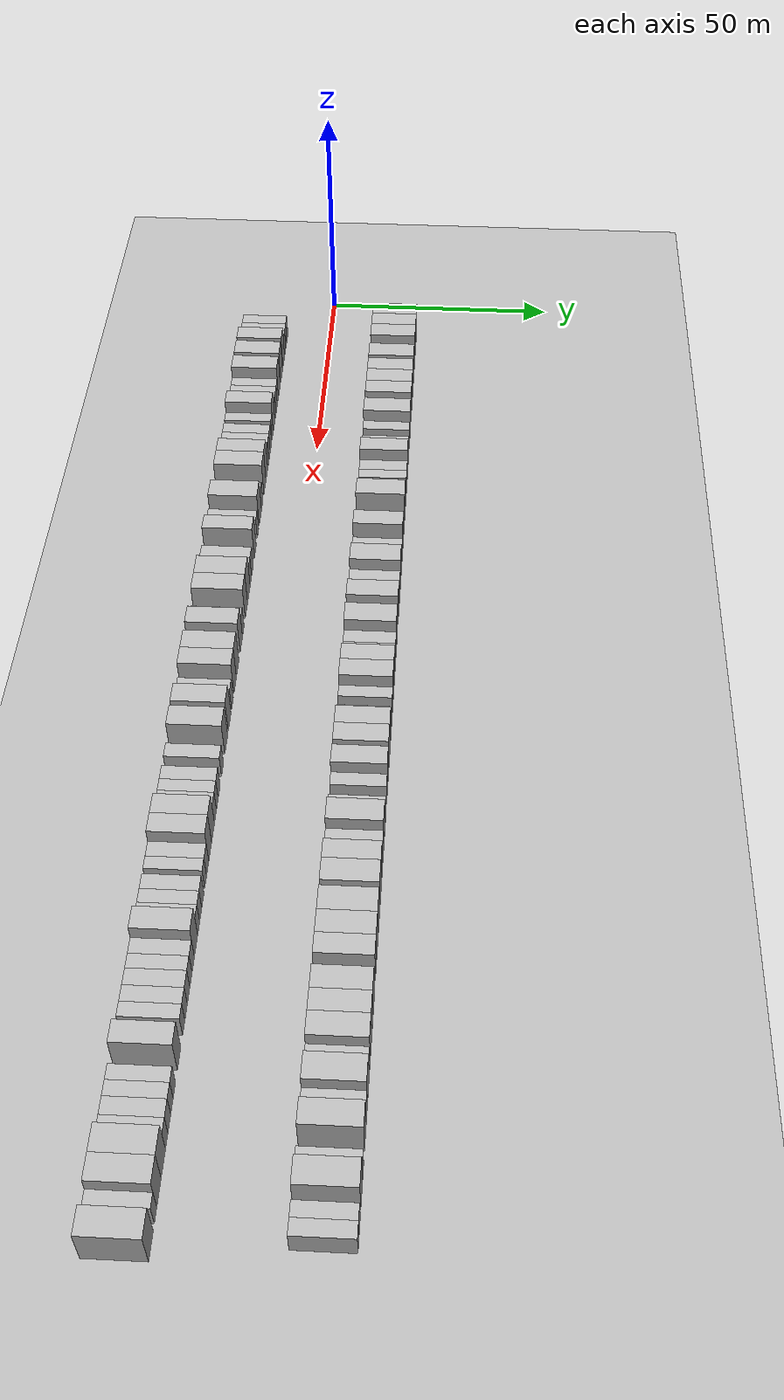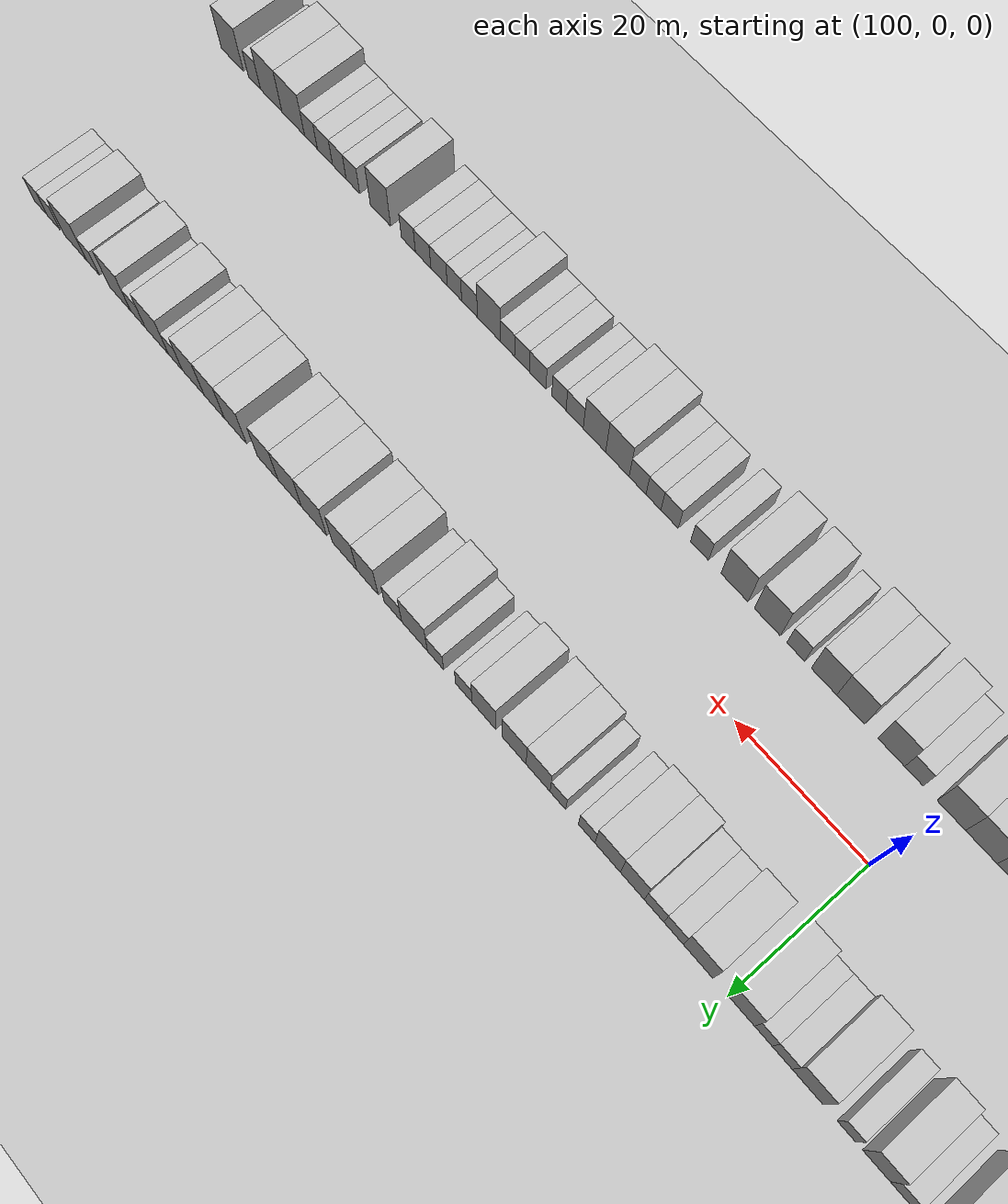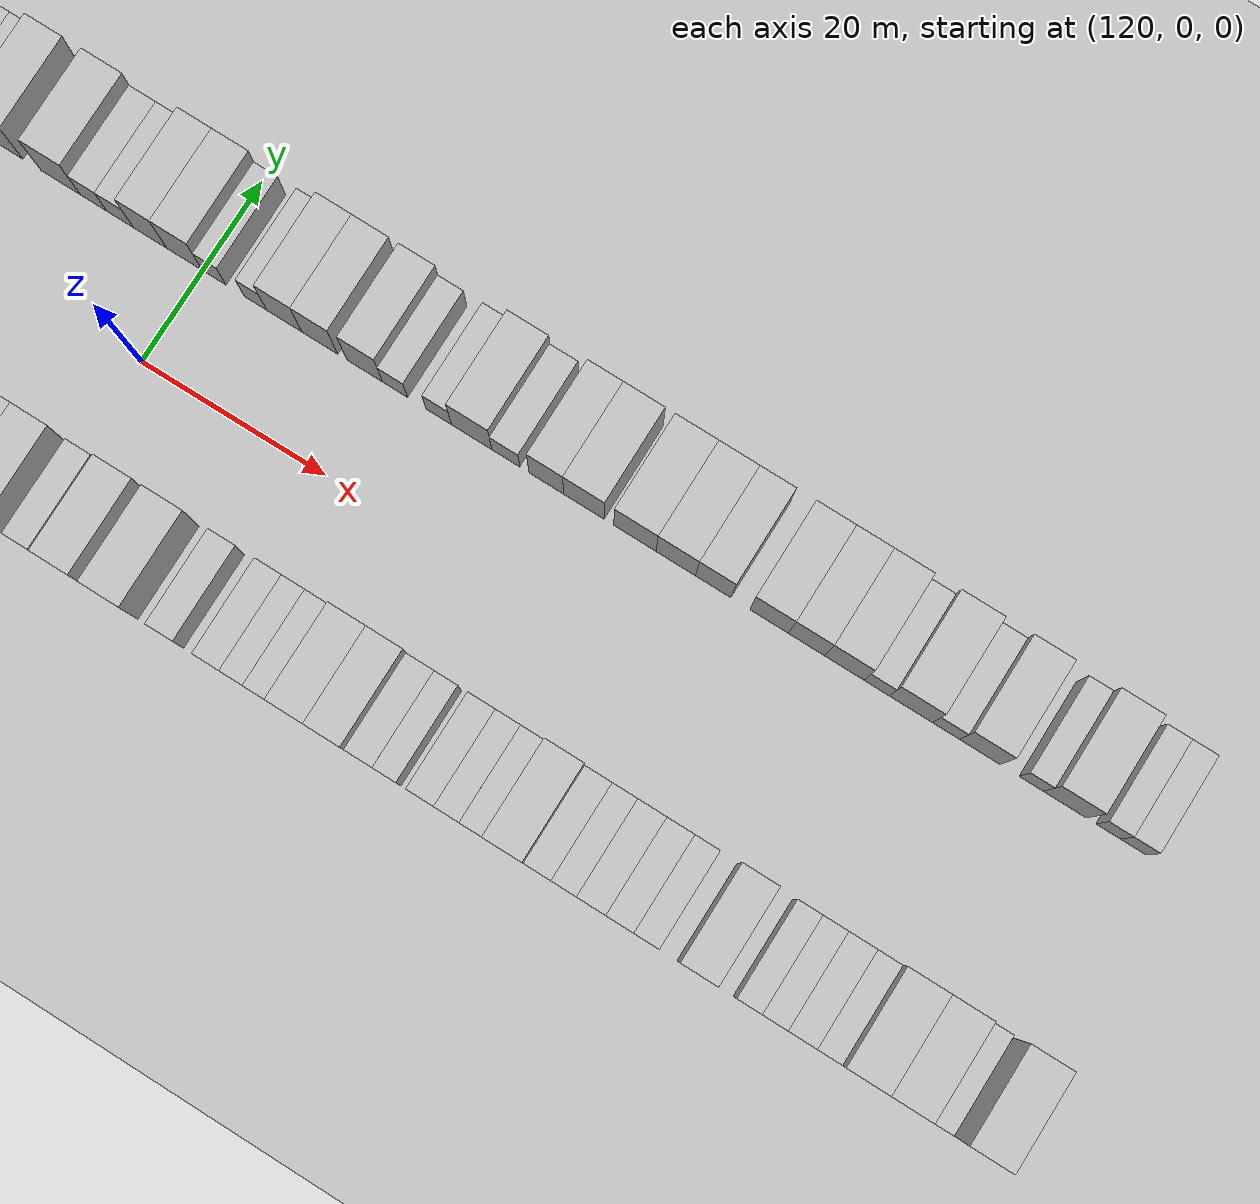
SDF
<?xml version="1.0" encoding="utf-8"?>

<sdf version="1.6">

   <world name="default">

      <gui fullscreen="0">

         <camera name="user_camera">

            <pose>-15 0 4.57585 0 0 0</pose>

            <view_controller>orbit</view_controller>

         </camera>

      </gui>

      <scene>

         <sky>

           <clouds>

             <speed>12</speed>

           </clouds>

         </sky>

         <ambient>0.4 0.4 0.4 1</ambient>

         <background>0.7 0.7 0.7 1</background>

         <shadows>1</shadows>

      </scene>

      <gravity>0 0 -9.8066</gravity>

      <magnetic_field>6e-06 2.3e-05 -4.2e-05</magnetic_field>

      <physics default="0" name="default_physics" type="ode">

         <ode>

            <solver>

               <type>quick</type>

               <iters>10</iters>

               <sor>1.0</sor>

               <use_dynamic_moi_rescaling>0</use_dynamic_moi_rescaling>

            </solver>

            <constraints>

               <cfm>0</cfm>

               <erp>0.2</erp>

               <contact_max_correcting_vel>100</contact_max_correcting_vel>

               <contact_surface_layer>0.001</contact_surface_layer>

            </constraints>

         </ode>

         <max_step_size>0.004</max_step_size>

         <real_time_factor>1</real_time_factor>

         <real_time_update_rate>250</real_time_update_rate>

      </physics>

      <light name="sun" type="directional">

         <cast_shadows>1</cast_shadows>

         <pose>0 0 10 0 0 0</pose>

         <diffuse>0.8 0.8 0.8 1</diffuse>

         <specular>0.2 0.2 0.2 1</specular>

         <attenuation>

            <range>1000</range>

            <constant>0.9</constant>

            <linear>0.01</linear>

            <quadratic>0.001</quadratic>

         </attenuation>

         <direction>-0.5 0.1 -0.9</direction>

      </light>

      <include>

         <name>ground_plane_1</name>

         <uri>model://HANNAS_ground_plane</uri>

         <pose>0 0 0  0 0 0</pose>

      </include>

      <include>

         <name>ground_plane_2</name>

         <uri>model://HANNAS_ground_plane</uri>

         <pose>100 0 0  0 0 0</pose>

      </include>

      <model name="building_1">

         <static>1</static>

         <pose frame="">11.8060 15.0000 0 0.000000 0.000000 1.570796</pose>

         <link name="link">

            <pose frame="">0 0 4.50 0 0 0</pose>

            <collision name="collision">

               <geometry>

                  <box>

                     <size>10.0000 3.6119 9.0000</size>

                  </box>

               </geometry>

               <max_contacts>10</max_contacts>

               <surface>

                  <contact>

                     <ode/>

                  </contact>

                  <bounce/>

                  <friction>

                     <torsional>

                        <ode/>

                     </torsional>

                     <ode/>

                  </friction>

               </surface>

            </collision>

            <visual name="visual">

               <cast_shadows>0</cast_shadows>

               <geometry>

                  <box>

                     <size>10.0000 3.6119 9.0000</size>

                  </box>

               </geometry>

               <material>

                  <script>

                     <uri>model://HANNAS_wall/materials/scripts</uri>

                     <uri>model://HANNAS_wall/materials/textures</uri>

                     <name>vrc/HANNAS_wall</name>

                  </script>

               </material>

            </visual>

            <self_collide>0</self_collide>

            <enable_wind>0</enable_wind>

            <kinematic>0</kinematic>

         </link>

      </model>

      <model name="building_2">

         <static>1</static>

         <pose frame="">15.5486 15.0000 0 0.000000 0.000000 1.570796</pose>

         <link name="link">

            <pose frame="">0 0 4.50 0 0 0</pose>

            <collision name="collision">

               <geometry>

                  <box>

                     <size>10.0000 3.8733 9.0000</size>

                  </box>

               </geometry>

               <max_contacts>10</max_contacts>

               <surface>

                  <contact>

                     <ode/>

                  </contact>

                  <bounce/>

                  <friction>

                     <torsional>

                        <ode/>

                     </torsional>

                     <ode/>

                  </friction>

               </surface>

            </collision>

            <visual name="visual">

               <cast_shadows>0</cast_shadows>

               <geometry>

                  <box>

                     <size>10.0000 3.8733 9.0000</size>

                  </box>

               </geometry>

               <material>

                  <script>

                     <uri>model://HANNAS_wall/materials/scripts</uri>

                     <uri>model://HANNAS_wall/materials/textures</uri>

                     <name>vrc/HANNAS_wall</name>

                  </script>

               </material>

            </visual>

            <self_collide>0</self_collide>

            <enable_wind>0</enable_wind>

            <kinematic>0</kinematic>

         </link>

      </model>

      <model name="building_3">

         <static>1</static>

         <pose frame="">19.5123 15.0000 0 0.000000 0.000000 1.570796</pose>

         <link name="link">

            <pose frame="">0 0 4.50 0 0 0</pose>

            <collision name="collision">

               <geometry>

                  <box>

                     <size>10.0000 4.0541 9.0000</size>

                  </box>

               </geometry>

               <max_contacts>10</max_contacts>

               <surface>

                  <contact>

                     <ode/>

                  </contact>

                  <bounce/>

                  <friction>

                     <torsional>

                        <ode/>

                     </torsional>

                     <ode/>

                  </friction>

               </surface>

            </collision>

            <visual name="visual">

               <cast_shadows>0</cast_shadows>

               <geometry>

                  <box>

                     <size>10.0000 4.0541 9.0000</size>

                  </box>

               </geometry>

               <material>

                  <script>

                     <uri>model://HANNAS_wall/materials/scripts</uri>

                     <uri>model://HANNAS_wall/materials/textures</uri>

                     <name>vrc/HANNAS_wall</name>

                  </script>

               </material>

            </visual>

            <self_collide>0</self_collide>

            <enable_wind>0</enable_wind>

            <kinematic>0</kinematic>

         </link>

      </model>

      <model name="building_4">

         <static>1</static>

         <pose frame="">22.9831 15.0000 0 0.000000 0.000000 1.570796</pose>

         <link name="link">

            <pose frame="">0 0 3.00 0 0 0</pose>

            <collision name="collision">

               <geometry>

                  <box>

                     <size>10.0000 2.8875 6.0000</size>

                  </box>

               </geometry>

               <max_contacts>10</max_contacts>

               <surface>

                  <contact>

                     <ode/>

                  </contact>

                  <bounce/>

                  <friction>

                     <torsional>

                        <ode/>

                     </torsional>

                     <ode/>

                  </friction>

               </surface>

            </collision>

            <visual name="visual">

               <cast_shadows>0</cast_shadows>

               <geometry>

                  <box>

                     <size>10.0000 2.8875 6.0000</size>

                  </box>

               </geometry>

               <material>

                  <script>

                     <uri>model://HANNAS_wall/materials/scripts</uri>

                     <uri>model://HANNAS_wall/materials/textures</uri>

                     <name>vrc/HANNAS_wall</name>

                  </script>

               </material>

            </visual>

            <self_collide>0</self_collide>

            <enable_wind>0</enable_wind>

            <kinematic>0</kinematic>

         </link>

      </model>

      <model name="building_5">

         <static>1</static>

         <pose frame="">26.4760 15.0000 0 0.000000 0.000000 1.570796</pose>

         <link name="link">

            <pose frame="">0 0 4.50 0 0 0</pose>

            <collision name="collision">

               <geometry>

                  <box>

                     <size>10.0000 4.0983 9.0000</size>

                  </box>

               </geometry>

               <max_contacts>10</max_contacts>

               <surface>

                  <contact>

                     <ode/>

                  </contact>

                  <bounce/>

                  <friction>

                     <torsional>

                        <ode/>

                     </torsional>

                     <ode/>

                  </friction>

               </surface>

            </collision>

            <visual name="visual">

               <cast_shadows>0</cast_shadows>

               <geometry>

                  <box>

                     <size>10.0000 4.0983 9.0000</size>

                  </box>

               </geometry>

               <material>

                  <script>

                     <uri>model://HANNAS_wall/materials/scripts</uri>

                     <uri>model://HANNAS_wall/materials/textures</uri>

                     <name>vrc/HANNAS_wall</name>

                  </script>

               </material>

            </visual>

            <self_collide>0</self_collide>

            <enable_wind>0</enable_wind>

            <kinematic>0</kinematic>

         </link>

      </model>

      <model name="building_6">

         <static>1</static>

         <pose frame="">31.3769 15.0000 0 0.000000 0.000000 1.570796</pose>

         <link name="link">

            <pose frame="">0 0 4.50 0 0 0</pose>

            <collision name="collision">

               <geometry>

                  <box>

                     <size>10.0000 3.7035 9.0000</size>

                  </box>

               </geometry>

               <max_contacts>10</max_contacts>

               <surface>

                  <contact>

                     <ode/>

                  </contact>

                  <bounce/>

                  <friction>

                     <torsional>

                        <ode/>

                     </torsional>

                     <ode/>

                  </friction>

               </surface>

            </collision>

            <visual name="visual">

               <cast_shadows>0</cast_shadows>

               <geometry>

                  <box>

                     <size>10.0000 3.7035 9.0000</size>

                  </box>

               </geometry>

               <material>

                  <script>

                     <uri>model://HANNAS_wall/materials/scripts</uri>

                     <uri>model://HANNAS_wall/materials/textures</uri>

                     <name>vrc/HANNAS_wall</name>

                  </script>

               </material>

            </visual>

            <self_collide>0</self_collide>

            <enable_wind>0</enable_wind>

            <kinematic>0</kinematic>

         </link>

      </model>

      <model name="building_7">

         <static>1</static>

         <pose frame="">35.2094 15.0000 0 0.000000 0.000000 1.570796</pose>

         <link name="link">

            <pose frame="">0 0 4.50 0 0 0</pose>

            <collision name="collision">

               <geometry>

                  <box>

                     <size>10.0000 3.9614 9.0000</size>

                  </box>

               </geometry>

               <max_contacts>10</max_contacts>

               <surface>

                  <contact>

                     <ode/>

                  </contact>

                  <bounce/>

                  <friction>

                     <torsional>

                        <ode/>

                     </torsional>

                     <ode/>

                  </friction>

               </surface>

            </collision>

            <visual name="visual">

               <cast_shadows>0</cast_shadows>

               <geometry>

                  <box>

                     <size>10.0000 3.9614 9.0000</size>

                  </box>

               </geometry>

               <material>

                  <script>

                     <uri>model://HANNAS_wall/materials/scripts</uri>

                     <uri>model://HANNAS_wall/materials/textures</uri>

                     <name>vrc/HANNAS_wall</name>

                  </script>

               </material>

            </visual>

            <self_collide>0</self_collide>

            <enable_wind>0</enable_wind>

            <kinematic>0</kinematic>

         </link>

      </model>

      <model name="building_8">

         <static>1</static>

         <pose frame="">39.0596 15.0000 0 0.000000 0.000000 1.570796</pose>

         <link name="link">

            <pose frame="">0 0 4.50 0 0 0</pose>

            <collision name="collision">

               <geometry>

                  <box>

                     <size>10.0000 3.7391 9.0000</size>

                  </box>

               </geometry>

               <max_contacts>10</max_contacts>

               <surface>

                  <contact>

                     <ode/>

                  </contact>

                  <bounce/>

                  <friction>

                     <torsional>

                        <ode/>

                     </torsional>

                     <ode/>

                  </friction>

               </surface>

            </collision>

            <visual name="visual">

               <cast_shadows>0</cast_shadows>

               <geometry>

                  <box>

                     <size>10.0000 3.7391 9.0000</size>

                  </box>

               </geometry>

               <material>

                  <script>

                     <uri>model://HANNAS_wall/materials/scripts</uri>

                     <uri>model://HANNAS_wall/materials/textures</uri>

                     <name>vrc/HANNAS_wall</name>

                  </script>

               </material>

            </visual>

            <self_collide>0</self_collide>

            <enable_wind>0</enable_wind>

            <kinematic>0</kinematic>

         </link>

      </model>

      <model name="building_9">

         <static>1</static>

         <pose frame="">45.0208 15.0000 0 0.000000 0.000000 1.570796</pose>

         <link name="link">

            <pose frame="">0 0 4.50 0 0 0</pose>

            <collision name="collision">

               <geometry>

                  <box>

                     <size>10.0000 4.1831 9.0000</size>

                  </box>

               </geometry>

               <max_contacts>10</max_contacts>

               <surface>

                  <contact>

                     <ode/>

                  </contact>

                  <bounce/>

                  <friction>

                     <torsional>

                        <ode/>

                     </torsional>

                     <ode/>

                  </friction>

               </surface>

            </collision>

            <visual name="visual">

               <cast_shadows>0</cast_shadows>

               <geometry>

                  <box>

                     <size>10.0000 4.1831 9.0000</size>

                  </box>

               </geometry>

               <material>

                  <script>

                     <uri>model://HANNAS_wall/materials/scripts</uri>

                     <uri>model://HANNAS_wall/materials/textures</uri>

                     <name>vrc/HANNAS_wall</name>

                  </script>

               </material>

            </visual>

            <self_collide>0</self_collide>

            <enable_wind>0</enable_wind>

            <kinematic>0</kinematic>

         </link>

      </model>

      <model name="building_10">

         <static>1</static>

         <pose frame="">48.4158 15.0000 0 0.000000 0.000000 1.570796</pose>

         <link name="link">

            <pose frame="">0 0 3.00 0 0 0</pose>

            <collision name="collision">

               <geometry>

                  <box>

                     <size>10.0000 2.6068 6.0000</size>

                  </box>

               </geometry>

               <max_contacts>10</max_contacts>

               <surface>

                  <contact>

                     <ode/>

                  </contact>

                  <bounce/>

                  <friction>

                     <torsional>

                        <ode/>

                     </torsional>

                     <ode/>

                  </friction>

               </surface>

            </collision>

            <visual name="visual">

               <cast_shadows>0</cast_shadows>

               <geometry>

                  <box>

                     <size>10.0000 2.6068 6.0000</size>

                  </box>

               </geometry>

               <material>

                  <script>

                     <uri>model://HANNAS_wall/materials/scripts</uri>

                     <uri>model://HANNAS_wall/materials/textures</uri>

                     <name>vrc/HANNAS_wall</name>

                  </script>

               </material>

            </visual>

            <self_collide>0</self_collide>

            <enable_wind>0</enable_wind>

            <kinematic>0</kinematic>

         </link>

      </model>

      <model name="building_11">

         <static>1</static>

         <pose frame="">53.2167 15.0000 0 0.000000 0.000000 1.570796</pose>

         <link name="link">

            <pose frame="">0 0 3.00 0 0 0</pose>

            <collision name="collision">

               <geometry>

                  <box>

                     <size>10.0000 2.9951 6.0000</size>

                  </box>

               </geometry>

               <max_contacts>10</max_contacts>

               <surface>

                  <contact>

                     <ode/>

                  </contact>

                  <bounce/>

                  <friction>

                     <torsional>

                        <ode/>

                     </torsional>

                     <ode/>

                  </friction>

               </surface>

            </collision>

            <visual name="visual">

               <cast_shadows>0</cast_shadows>

               <geometry>

                  <box>

                     <size>10.0000 2.9951 6.0000</size>

                  </box>

               </geometry>

               <material>

                  <script>

                     <uri>model://HANNAS_wall/materials/scripts</uri>

                     <uri>model://HANNAS_wall/materials/textures</uri>

                     <name>vrc/HANNAS_wall</name>

                  </script>

               </material>

            </visual>

            <self_collide>0</self_collide>

            <enable_wind>0</enable_wind>

            <kinematic>0</kinematic>

         </link>

      </model>

      <model name="building_12">

         <static>1</static>

         <pose frame="">57.5387 15.0000 0 0.000000 0.000000 1.570796</pose>

         <link name="link">

            <pose frame="">0 0 4.50 0 0 0</pose>

            <collision name="collision">

               <geometry>

                  <box>

                     <size>10.0000 3.6490 9.0000</size>

                  </box>

               </geometry>

               <max_contacts>10</max_contacts>

               <surface>

                  <contact>

                     <ode/>

                  </contact>

                  <bounce/>

                  <friction>

                     <torsional>

                        <ode/>

                     </torsional>

                     <ode/>

                  </friction>

               </surface>

            </collision>

            <visual name="visual">

               <cast_shadows>0</cast_shadows>

               <geometry>

                  <box>

                     <size>10.0000 3.6490 9.0000</size>

                  </box>

               </geometry>

               <material>

                  <script>

                     <uri>model://HANNAS_wall/materials/scripts</uri>

                     <uri>model://HANNAS_wall/materials/textures</uri>

                     <name>vrc/HANNAS_wall</name>

                  </script>

               </material>

            </visual>

            <self_collide>0</self_collide>

            <enable_wind>0</enable_wind>

            <kinematic>0</kinematic>

         </link>

      </model>

      <model name="building_13">

         <static>1</static>

         <pose frame="">60.8177 15.0000 0 0.000000 0.000000 1.570796</pose>

         <link name="link">

            <pose frame="">0 0 3.00 0 0 0</pose>

            <collision name="collision">

               <geometry>

                  <box>

                     <size>10.0000 2.9090 6.0000</size>

                  </box>

               </geometry>

               <max_contacts>10</max_contacts>

               <surface>

                  <contact>

                     <ode/>

                  </contact>

                  <bounce/>

                  <friction>

                     <torsional>

                        <ode/>

                     </torsional>

                     <ode/>

                  </friction>

               </surface>

            </collision>

            <visual name="visual">

               <cast_shadows>0</cast_shadows>

               <geometry>

                  <box>

                     <size>10.0000 2.9090 6.0000</size>

                  </box>

               </geometry>

               <material>

                  <script>

                     <uri>model://HANNAS_wall/materials/scripts</uri>

                     <uri>model://HANNAS_wall/materials/textures</uri>

                     <name>vrc/HANNAS_wall</name>

                  </script>

               </material>

            </visual>

            <self_collide>0</self_collide>

            <enable_wind>0</enable_wind>

            <kinematic>0</kinematic>

         </link>

      </model>

      <model name="building_14">

         <static>1</static>

         <pose frame="">63.4770 15.0000 0 0.000000 0.000000 1.570796</pose>

         <link name="link">

            <pose frame="">0 0 3.00 0 0 0</pose>

            <collision name="collision">

               <geometry>

                  <box>

                     <size>10.0000 2.4096 6.0000</size>

                  </box>

               </geometry>

               <max_contacts>10</max_contacts>

               <surface>

                  <contact>

                     <ode/>

                  </contact>

                  <bounce/>

                  <friction>

                     <torsional>

                        <ode/>

                     </torsional>

                     <ode/>

                  </friction>

               </surface>

            </collision>

            <visual name="visual">

               <cast_shadows>0</cast_shadows>

               <geometry>

                  <box>

                     <size>10.0000 2.4096 6.0000</size>

                  </box>

               </geometry>

               <material>

                  <script>

                     <uri>model://HANNAS_wall/materials/scripts</uri>

                     <uri>model://HANNAS_wall/materials/textures</uri>

                     <name>vrc/HANNAS_wall</name>

                  </script>

               </material>

            </visual>

            <self_collide>0</self_collide>

            <enable_wind>0</enable_wind>

            <kinematic>0</kinematic>

         </link>

      </model>

      <model name="building_15">

         <static>1</static>

         <pose frame="">66.9053 15.0000 0 0.000000 0.000000 1.570796</pose>

         <link name="link">

            <pose frame="">0 0 3.00 0 0 0</pose>

            <collision name="collision">

               <geometry>

                  <box>

                     <size>10.0000 2.4470 6.0000</size>

                  </box>

               </geometry>

               <max_contacts>10</max_contacts>

               <surface>

                  <contact>

                     <ode/>

                  </contact>

                  <bounce/>

                  <friction>

                     <torsional>

                        <ode/>

                     </torsional>

                     <ode/>

                  </friction>

               </surface>

            </collision>

            <visual name="visual">

               <cast_shadows>0</cast_shadows>

               <geometry>

                  <box>

                     <size>10.0000 2.4470 6.0000</size>

                  </box>

               </geometry>

               <material>

                  <script>

                     <uri>model://HANNAS_wall/materials/scripts</uri>

                     <uri>model://HANNAS_wall/materials/textures</uri>

                     <name>vrc/HANNAS_wall</name>

                  </script>

               </material>

            </visual>

            <self_collide>0</self_collide>

            <enable_wind>0</enable_wind>

            <kinematic>0</kinematic>

         </link>

      </model>

      <model name="building_16">

         <static>1</static>

         <pose frame="">70.2902 15.0000 0 0.000000 0.000000 1.570796</pose>

         <link name="link">

            <pose frame="">0 0 4.50 0 0 0</pose>

            <collision name="collision">

               <geometry>

                  <box>

                     <size>10.0000 4.3228 9.0000</size>

                  </box>

               </geometry>

               <max_contacts>10</max_contacts>

               <surface>

                  <contact>

                     <ode/>

                  </contact>

                  <bounce/>

                  <friction>

                     <torsional>

                        <ode/>

                     </torsional>

                     <ode/>

                  </friction>

               </surface>

            </collision>

            <visual name="visual">

               <cast_shadows>0</cast_shadows>

               <geometry>

                  <box>

                     <size>10.0000 4.3228 9.0000</size>

                  </box>

               </geometry>

               <material>

                  <script>

                     <uri>model://HANNAS_wall/materials/scripts</uri>

                     <uri>model://HANNAS_wall/materials/textures</uri>

                     <name>vrc/HANNAS_wall</name>

                  </script>

               </material>

            </visual>

            <self_collide>0</self_collide>

            <enable_wind>0</enable_wind>

            <kinematic>0</kinematic>

         </link>

      </model>

      <model name="building_17">

         <static>1</static>

         <pose frame="">75.8866 15.0000 0 0.000000 0.000000 1.570796</pose>

         <link name="link">

            <pose frame="">0 0 3.00 0 0 0</pose>

            <collision name="collision">

               <geometry>

                  <box>

                     <size>10.0000 2.8701 6.0000</size>

                  </box>

               </geometry>

               <max_contacts>10</max_contacts>

               <surface>

                  <contact>

                     <ode/>

                  </contact>

                  <bounce/>

                  <friction>

                     <torsional>

                        <ode/>

                     </torsional>

                     <ode/>

                  </friction>

               </surface>

            </collision>

            <visual name="visual">

               <cast_shadows>0</cast_shadows>

               <geometry>

                  <box>

                     <size>10.0000 2.8701 6.0000</size>

                  </box>

               </geometry>

               <material>

                  <script>

                     <uri>model://HANNAS_wall/materials/scripts</uri>

                     <uri>model://HANNAS_wall/materials/textures</uri>

                     <name>vrc/HANNAS_wall</name>

                  </script>

               </material>

            </visual>

            <self_collide>0</self_collide>

            <enable_wind>0</enable_wind>

            <kinematic>0</kinematic>

         </link>

      </model>

      <model name="building_18">

         <static>1</static>

         <pose frame="">79.2001 15.0000 0 0.000000 0.000000 1.570796</pose>

         <link name="link">

            <pose frame="">0 0 4.50 0 0 0</pose>

            <collision name="collision">

               <geometry>

                  <box>

                     <size>10.0000 3.7569 9.0000</size>

                  </box>

               </geometry>

               <max_contacts>10</max_contacts>

               <surface>

                  <contact>

                     <ode/>

                  </contact>

                  <bounce/>

                  <friction>

                     <torsional>

                        <ode/>

                     </torsional>

                     <ode/>

                  </friction>

               </surface>

            </collision>

            <visual name="visual">

               <cast_shadows>0</cast_shadows>

               <geometry>

                  <box>

                     <size>10.0000 3.7569 9.0000</size>

                  </box>

               </geometry>

               <material>

                  <script>

                     <uri>model://HANNAS_wall/materials/scripts</uri>

                     <uri>model://HANNAS_wall/materials/textures</uri>

                     <name>vrc/HANNAS_wall</name>

                  </script>

               </material>

            </visual>

            <self_collide>0</self_collide>

            <enable_wind>0</enable_wind>

            <kinematic>0</kinematic>

         </link>

      </model>

      <model name="building_19">

         <static>1</static>

         <pose frame="">83.3253 15.0000 0 0.000000 0.000000 1.570796</pose>

         <link name="link">

            <pose frame="">0 0 3.00 0 0 0</pose>

            <collision name="collision">

               <geometry>

                  <box>

                     <size>10.0000 2.4935 6.0000</size>

                  </box>

               </geometry>

               <max_contacts>10</max_contacts>

               <surface>

                  <contact>

                     <ode/>

                  </contact>

                  <bounce/>

                  <friction>

                     <torsional>

                        <ode/>

                     </torsional>

                     <ode/>

                  </friction>

               </surface>

            </collision>

            <visual name="visual">

               <cast_shadows>0</cast_shadows>

               <geometry>

                  <box>

                     <size>10.0000 2.4935 6.0000</size>

                  </box>

               </geometry>

               <material>

                  <script>

                     <uri>model://HANNAS_wall/materials/scripts</uri>

                     <uri>model://HANNAS_wall/materials/textures</uri>

                     <name>vrc/HANNAS_wall</name>

                  </script>

               </material>

            </visual>

            <self_collide>0</self_collide>

            <enable_wind>0</enable_wind>

            <kinematic>0</kinematic>

         </link>

      </model>

      <model name="building_20">

         <static>1</static>

         <pose frame="">88.7367 15.0000 0 0.000000 0.000000 1.570796</pose>

         <link name="link">

            <pose frame="">0 0 4.50 0 0 0</pose>

            <collision name="collision">

               <geometry>

                  <box>

                     <size>10.0000 4.3294 9.0000</size>

                  </box>

               </geometry>

               <max_contacts>10</max_contacts>

               <surface>

                  <contact>

                     <ode/>

                  </contact>

                  <bounce/>

                  <friction>

                     <torsional>

                        <ode/>

                     </torsional>

                     <ode/>

                  </friction>

               </surface>

            </collision>

            <visual name="visual">

               <cast_shadows>0</cast_shadows>

               <geometry>

                  <box>

                     <size>10.0000 4.3294 9.0000</size>

                  </box>

               </geometry>

               <material>

                  <script>

                     <uri>model://HANNAS_wall/materials/scripts</uri>

                     <uri>model://HANNAS_wall/materials/textures</uri>

                     <name>vrc/HANNAS_wall</name>

                  </script>

               </material>

            </visual>

            <self_collide>0</self_collide>

            <enable_wind>0</enable_wind>

            <kinematic>0</kinematic>

         </link>

      </model>

      <model name="building_21">

         <static>1</static>

         <pose frame="">92.3291 15.0000 0 0.000000 0.000000 1.570796</pose>

         <link name="link">

            <pose frame="">0 0 3.00 0 0 0</pose>

            <collision name="collision">

               <geometry>

                  <box>

                     <size>10.0000 2.8554 6.0000</size>

                  </box>

               </geometry>

               <max_contacts>10</max_contacts>

               <surface>

                  <contact>

                     <ode/>

                  </contact>

                  <bounce/>

                  <friction>

                     <torsional>

                        <ode/>

                     </torsional>

                     <ode/>

                  </friction>

               </surface>

            </collision>

            <visual name="visual">

               <cast_shadows>0</cast_shadows>

               <geometry>

                  <box>

                     <size>10.0000 2.8554 6.0000</size>

                  </box>

               </geometry>

               <material>

                  <script>

                     <uri>model://HANNAS_wall/materials/scripts</uri>

                     <uri>model://HANNAS_wall/materials/textures</uri>

                     <name>vrc/HANNAS_wall</name>

                  </script>

               </material>

            </visual>

            <self_collide>0</self_collide>

            <enable_wind>0</enable_wind>

            <kinematic>0</kinematic>

         </link>

      </model>

      <model name="building_22">

         <static>1</static>

         <pose frame="">95.0133 15.0000 0 0.000000 0.000000 1.570796</pose>

         <link name="link">

            <pose frame="">0 0 3.00 0 0 0</pose>

            <collision name="collision">

               <geometry>

                  <box>

                     <size>10.0000 2.5129 6.0000</size>

                  </box>

               </geometry>

               <max_contacts>10</max_contacts>

               <surface>

                  <contact>

                     <ode/>

                  </contact>

                  <bounce/>

                  <friction>

                     <torsional>

                        <ode/>

                     </torsional>

                     <ode/>

                  </friction>

               </surface>

            </collision>

            <visual name="visual">

               <cast_shadows>0</cast_shadows>

               <geometry>

                  <box>

                     <size>10.0000 2.5129 6.0000</size>

                  </box>

               </geometry>

               <material>

                  <script>

                     <uri>model://HANNAS_wall/materials/scripts</uri>

                     <uri>model://HANNAS_wall/materials/textures</uri>

                     <name>vrc/HANNAS_wall</name>

                  </script>

               </material>

            </visual>

            <self_collide>0</self_collide>

            <enable_wind>0</enable_wind>

            <kinematic>0</kinematic>

         </link>

      </model>

      <model name="building_23">

         <static>1</static>

         <pose frame="">98.2925 15.0000 0 0.000000 0.000000 1.570796</pose>

         <link name="link">

            <pose frame="">0 0 4.50 0 0 0</pose>

            <collision name="collision">

               <geometry>

                  <box>

                     <size>10.0000 4.0456 9.0000</size>

                  </box>

               </geometry>

               <max_contacts>10</max_contacts>

               <surface>

                  <contact>

                     <ode/>

                  </contact>

                  <bounce/>

                  <friction>

                     <torsional>

                        <ode/>

                     </torsional>

                     <ode/>

                  </friction>

               </surface>

            </collision>

            <visual name="visual">

               <cast_shadows>0</cast_shadows>

               <geometry>

                  <box>

                     <size>10.0000 4.0456 9.0000</size>

                  </box>

               </geometry>

               <material>

                  <script>

                     <uri>model://HANNAS_wall/materials/scripts</uri>

                     <uri>model://HANNAS_wall/materials/textures</uri>

                     <name>vrc/HANNAS_wall</name>

                  </script>

               </material>

            </visual>

            <self_collide>0</self_collide>

            <enable_wind>0</enable_wind>

            <kinematic>0</kinematic>

         </link>

      </model>

      <model name="building_24">

         <static>1</static>

         <pose frame="">104.5154 15.0000 0 0.000000 0.000000 1.570796</pose>

         <link name="link">

            <pose frame="">0 0 4.50 0 0 0</pose>

            <collision name="collision">

               <geometry>

                  <box>

                     <size>10.0000 4.4003 9.0000</size>

                  </box>

               </geometry>

               <max_contacts>10</max_contacts>

               <surface>

                  <contact>

                     <ode/>

                  </contact>

                  <bounce/>

                  <friction>

                     <torsional>

                        <ode/>

                     </torsional>

                     <ode/>

                  </friction>

               </surface>

            </collision>

            <visual name="visual">

               <cast_shadows>0</cast_shadows>

               <geometry>

                  <box>

                     <size>10.0000 4.4003 9.0000</size>

                  </box>

               </geometry>

               <material>

                  <script>

                     <uri>model://HANNAS_wall/materials/scripts</uri>

                     <uri>model://HANNAS_wall/materials/textures</uri>

                     <name>vrc/HANNAS_wall</name>

                  </script>

               </material>

            </visual>

            <self_collide>0</self_collide>

            <enable_wind>0</enable_wind>

            <kinematic>0</kinematic>

         </link>

      </model>

      <model name="building_25">

         <static>1</static>

         <pose frame="">108.1630 15.0000 0 0.000000 0.000000 1.570796</pose>

         <link name="link">

            <pose frame="">0 0 3.00 0 0 0</pose>

            <collision name="collision">

               <geometry>

                  <box>

                     <size>10.0000 2.8949 6.0000</size>

                  </box>

               </geometry>

               <max_contacts>10</max_contacts>

               <surface>

                  <contact>

                     <ode/>

                  </contact>

                  <bounce/>

                  <friction>

                     <torsional>

                        <ode/>

                     </torsional>

                     <ode/>

                  </friction>

               </surface>

            </collision>

            <visual name="visual">

               <cast_shadows>0</cast_shadows>

               <geometry>

                  <box>

                     <size>10.0000 2.8949 6.0000</size>

                  </box>

               </geometry>

               <material>

                  <script>

                     <uri>model://HANNAS_wall/materials/scripts</uri>

                     <uri>model://HANNAS_wall/materials/textures</uri>

                     <name>vrc/HANNAS_wall</name>

                  </script>

               </material>

            </visual>

            <self_collide>0</self_collide>

            <enable_wind>0</enable_wind>

            <kinematic>0</kinematic>

         </link>

      </model>

      <model name="building_26">

         <static>1</static>

         <pose frame="">111.0786 15.0000 0 0.000000 0.000000 1.570796</pose>

         <link name="link">

            <pose frame="">0 0 3.00 0 0 0</pose>

            <collision name="collision">

               <geometry>

                  <box>

                     <size>10.0000 2.9363 6.0000</size>

                  </box>

               </geometry>

               <max_contacts>10</max_contacts>

               <surface>

                  <contact>

                     <ode/>

                  </contact>

                  <bounce/>

                  <friction>

                     <torsional>

                        <ode/>

                     </torsional>

                     <ode/>

                  </friction>

               </surface>

            </collision>

            <visual name="visual">

               <cast_shadows>0</cast_shadows>

               <geometry>

                  <box>

                     <size>10.0000 2.9363 6.0000</size>

                  </box>

               </geometry>

               <material>

                  <script>

                     <uri>model://HANNAS_wall/materials/scripts</uri>

                     <uri>model://HANNAS_wall/materials/textures</uri>

                     <name>vrc/HANNAS_wall</name>

                  </script>

               </material>

            </visual>

            <self_collide>0</self_collide>

            <enable_wind>0</enable_wind>

            <kinematic>0</kinematic>

         </link>

      </model>

      <model name="building_27">

         <static>1</static>

         <pose frame="">114.3755 15.0000 0 0.000000 0.000000 1.570796</pose>

         <link name="link">

            <pose frame="">0 0 4.50 0 0 0</pose>

            <collision name="collision">

               <geometry>

                  <box>

                     <size>10.0000 3.6575 9.0000</size>

                  </box>

               </geometry>

               <max_contacts>10</max_contacts>

               <surface>

                  <contact>

                     <ode/>

                  </contact>

                  <bounce/>

                  <friction>

                     <torsional>

                        <ode/>

                     </torsional>

                     <ode/>

                  </friction>

               </surface>

            </collision>

            <visual name="visual">

               <cast_shadows>0</cast_shadows>

               <geometry>

                  <box>

                     <size>10.0000 3.6575 9.0000</size>

                  </box>

               </geometry>

               <material>

                  <script>

                     <uri>model://HANNAS_wall/materials/scripts</uri>

                     <uri>model://HANNAS_wall/materials/textures</uri>

                     <name>vrc/HANNAS_wall</name>

                  </script>

               </material>

            </visual>

            <self_collide>0</self_collide>

            <enable_wind>0</enable_wind>

            <kinematic>0</kinematic>

         </link>

      </model>

      <model name="building_28">

         <static>1</static>

         <pose frame="">118.1713 15.0000 0 0.000000 0.000000 1.570796</pose>

         <link name="link">

            <pose frame="">0 0 4.50 0 0 0</pose>

            <collision name="collision">

               <geometry>

                  <box>

                     <size>10.0000 3.9341 9.0000</size>

                  </box>

               </geometry>

               <max_contacts>10</max_contacts>

               <surface>

                  <contact>

                     <ode/>

                  </contact>

                  <bounce/>

                  <friction>

                     <torsional>

                        <ode/>

                     </torsional>

                     <ode/>

                  </friction>

               </surface>

            </collision>

            <visual name="visual">

               <cast_shadows>0</cast_shadows>

               <geometry>

                  <box>

                     <size>10.0000 3.9341 9.0000</size>

                  </box>

               </geometry>

               <material>

                  <script>

                     <uri>model://HANNAS_wall/materials/scripts</uri>

                     <uri>model://HANNAS_wall/materials/textures</uri>

                     <name>vrc/HANNAS_wall</name>

                  </script>

               </material>

            </visual>

            <self_collide>0</self_collide>

            <enable_wind>0</enable_wind>

            <kinematic>0</kinematic>

         </link>

      </model>

      <model name="building_29">

         <static>1</static>

         <pose frame="">121.4217 15.0000 0 0.000000 0.000000 1.570796</pose>

         <link name="link">

            <pose frame="">0 0 3.00 0 0 0</pose>

            <collision name="collision">

               <geometry>

                  <box>

                     <size>10.0000 2.5667 6.0000</size>

                  </box>

               </geometry>

               <max_contacts>10</max_contacts>

               <surface>

                  <contact>

                     <ode/>

                  </contact>

                  <bounce/>

                  <friction>

                     <torsional>

                        <ode/>

                     </torsional>

                     <ode/>

                  </friction>

               </surface>

            </collision>

            <visual name="visual">

               <cast_shadows>0</cast_shadows>

               <geometry>

                  <box>

                     <size>10.0000 2.5667 6.0000</size>

                  </box>

               </geometry>

               <material>

                  <script>

                     <uri>model://HANNAS_wall/materials/scripts</uri>

                     <uri>model://HANNAS_wall/materials/textures</uri>

                     <name>vrc/HANNAS_wall</name>

                  </script>

               </material>

            </visual>

            <self_collide>0</self_collide>

            <enable_wind>0</enable_wind>

            <kinematic>0</kinematic>

         </link>

      </model>

      <model name="building_30">

         <static>1</static>

         <pose frame="">125.9357 15.0000 0 0.000000 0.000000 1.570796</pose>

         <link name="link">

            <pose frame="">0 0 3.00 0 0 0</pose>

            <collision name="collision">

               <geometry>

                  <box>

                     <size>10.0000 2.4612 6.0000</size>

                  </box>

               </geometry>

               <max_contacts>10</max_contacts>

               <surface>

                  <contact>

                     <ode/>

                  </contact>

                  <bounce/>

                  <friction>

                     <torsional>

                        <ode/>

                     </torsional>

                     <ode/>

                  </friction>

               </surface>

            </collision>

            <visual name="visual">

               <cast_shadows>0</cast_shadows>

               <geometry>

                  <box>

                     <size>10.0000 2.4612 6.0000</size>

                  </box>

               </geometry>

               <material>

                  <script>

                     <uri>model://HANNAS_wall/materials/scripts</uri>

                     <uri>model://HANNAS_wall/materials/textures</uri>

                     <name>vrc/HANNAS_wall</name>

                  </script>

               </material>

            </visual>

            <self_collide>0</self_collide>

            <enable_wind>0</enable_wind>

            <kinematic>0</kinematic>

         </link>

      </model>

      <model name="building_31">

         <static>1</static>

         <pose frame="">129.0759 15.0000 0 0.000000 0.000000 1.570796</pose>

         <link name="link">

            <pose frame="">0 0 4.50 0 0 0</pose>

            <collision name="collision">

               <geometry>

                  <box>

                     <size>10.0000 3.8192 9.0000</size>

                  </box>

               </geometry>

               <max_contacts>10</max_contacts>

               <surface>

                  <contact>

                     <ode/>

                  </contact>

                  <bounce/>

                  <friction>

                     <torsional>

                        <ode/>

                     </torsional>

                     <ode/>

                  </friction>

               </surface>

            </collision>

            <visual name="visual">

               <cast_shadows>0</cast_shadows>

               <geometry>

                  <box>

                     <size>10.0000 3.8192 9.0000</size>

                  </box>

               </geometry>

               <material>

                  <script>

                     <uri>model://HANNAS_wall/materials/scripts</uri>

                     <uri>model://HANNAS_wall/materials/textures</uri>

                     <name>vrc/HANNAS_wall</name>

                  </script>

               </material>

            </visual>

            <self_collide>0</self_collide>

            <enable_wind>0</enable_wind>

            <kinematic>0</kinematic>

         </link>

      </model>

      <model name="building_32">

         <static>1</static>

         <pose frame="">132.9292 15.0000 0 0.000000 0.000000 1.570796</pose>

         <link name="link">

            <pose frame="">0 0 4.50 0 0 0</pose>

            <collision name="collision">

               <geometry>

                  <box>

                     <size>10.0000 3.8874 9.0000</size>

                  </box>

               </geometry>

               <max_contacts>10</max_contacts>

               <surface>

                  <contact>

                     <ode/>

                  </contact>

                  <bounce/>

                  <friction>

                     <torsional>

                        <ode/>

                     </torsional>

                     <ode/>

                  </friction>

               </surface>

            </collision>

            <visual name="visual">

               <cast_shadows>0</cast_shadows>

               <geometry>

                  <box>

                     <size>10.0000 3.8874 9.0000</size>

                  </box>

               </geometry>

               <material>

                  <script>

                     <uri>model://HANNAS_wall/materials/scripts</uri>

                     <uri>model://HANNAS_wall/materials/textures</uri>

                     <name>vrc/HANNAS_wall</name>

                  </script>

               </material>

            </visual>

            <self_collide>0</self_collide>

            <enable_wind>0</enable_wind>

            <kinematic>0</kinematic>

         </link>

      </model>

      <model name="building_33">

         <static>1</static>

         <pose frame="">137.8055 15.0000 0 0.000000 0.000000 1.570796</pose>

         <link name="link">

            <pose frame="">0 0 4.50 0 0 0</pose>

            <collision name="collision">

               <geometry>

                  <box>

                     <size>10.0000 3.8652 9.0000</size>

                  </box>

               </geometry>

               <max_contacts>10</max_contacts>

               <surface>

                  <contact>

                     <ode/>

                  </contact>

                  <bounce/>

                  <friction>

                     <torsional>

                        <ode/>

                     </torsional>

                     <ode/>

                  </friction>

               </surface>

            </collision>

            <visual name="visual">

               <cast_shadows>0</cast_shadows>

               <geometry>

                  <box>

                     <size>10.0000 3.8652 9.0000</size>

                  </box>

               </geometry>

               <material>

                  <script>

                     <uri>model://HANNAS_wall/materials/scripts</uri>

                     <uri>model://HANNAS_wall/materials/textures</uri>

                     <name>vrc/HANNAS_wall</name>

                  </script>

               </material>

            </visual>

            <self_collide>0</self_collide>

            <enable_wind>0</enable_wind>

            <kinematic>0</kinematic>

         </link>

      </model>

      <model name="building_34">

         <static>1</static>

         <pose frame="">141.0988 15.0000 0 0.000000 0.000000 1.570796</pose>

         <link name="link">

            <pose frame="">0 0 3.00 0 0 0</pose>

            <collision name="collision">

               <geometry>

                  <box>

                     <size>10.0000 2.7214 6.0000</size>

                  </box>

               </geometry>

               <max_contacts>10</max_contacts>

               <surface>

                  <contact>

                     <ode/>

                  </contact>

                  <bounce/>

                  <friction>

                     <torsional>

                        <ode/>

                     </torsional>

                     <ode/>

                  </friction>

               </surface>

            </collision>

            <visual name="visual">

               <cast_shadows>0</cast_shadows>

               <geometry>

                  <box>

                     <size>10.0000 2.7214 6.0000</size>

                  </box>

               </geometry>

               <material>

                  <script>

                     <uri>model://HANNAS_wall/materials/scripts</uri>

                     <uri>model://HANNAS_wall/materials/textures</uri>

                     <name>vrc/HANNAS_wall</name>

                  </script>

               </material>

            </visual>

            <self_collide>0</self_collide>

            <enable_wind>0</enable_wind>

            <kinematic>0</kinematic>

         </link>

      </model>

      <model name="building_35">

         <static>1</static>

         <pose frame="">145.8240 15.0000 0 0.000000 0.000000 1.570796</pose>

         <link name="link">

            <pose frame="">0 0 3.00 0 0 0</pose>

            <collision name="collision">

               <geometry>

                  <box>

                     <size>10.0000 2.7289 6.0000</size>

                  </box>

               </geometry>

               <max_contacts>10</max_contacts>

               <surface>

                  <contact>

                     <ode/>

                  </contact>

                  <bounce/>

                  <friction>

                     <torsional>

                        <ode/>

                     </torsional>

                     <ode/>

                  </friction>

               </surface>

            </collision>

            <visual name="visual">

               <cast_shadows>0</cast_shadows>

               <geometry>

                  <box>

                     <size>10.0000 2.7289 6.0000</size>

                  </box>

               </geometry>

               <material>

                  <script>

                     <uri>model://HANNAS_wall/materials/scripts</uri>

                     <uri>model://HANNAS_wall/materials/textures</uri>

                     <name>vrc/HANNAS_wall</name>

                  </script>

               </material>

            </visual>

            <self_collide>0</self_collide>

            <enable_wind>0</enable_wind>

            <kinematic>0</kinematic>

         </link>

      </model>

      <model name="building_36">

         <static>1</static>

         <pose frame="">149.3611 15.0000 0 0.000000 0.000000 1.570796</pose>

         <link name="link">

            <pose frame="">0 0 4.50 0 0 0</pose>

            <collision name="collision">

               <geometry>

                  <box>

                     <size>10.0000 4.3454 9.0000</size>

                  </box>

               </geometry>

               <max_contacts>10</max_contacts>

               <surface>

                  <contact>

                     <ode/>

                  </contact>

                  <bounce/>

                  <friction>

                     <torsional>

                        <ode/>

                     </torsional>

                     <ode/>

                  </friction>

               </surface>

            </collision>

            <visual name="visual">

               <cast_shadows>0</cast_shadows>

               <geometry>

                  <box>

                     <size>10.0000 4.3454 9.0000</size>

                  </box>

               </geometry>

               <material>

                  <script>

                     <uri>model://HANNAS_wall/materials/scripts</uri>

                     <uri>model://HANNAS_wall/materials/textures</uri>

                     <name>vrc/HANNAS_wall</name>

                  </script>

               </material>

            </visual>

            <self_collide>0</self_collide>

            <enable_wind>0</enable_wind>

            <kinematic>0</kinematic>

         </link>

      </model>

      <model name="building_37">

         <static>1</static>

         <pose frame="">153.0323 15.0000 0 0.000000 0.000000 1.570796</pose>

         <link name="link">

            <pose frame="">0 0 3.00 0 0 0</pose>

            <collision name="collision">

               <geometry>

                  <box>

                     <size>10.0000 2.9968 6.0000</size>

                  </box>

               </geometry>

               <max_contacts>10</max_contacts>

               <surface>

                  <contact>

                     <ode/>

                  </contact>

                  <bounce/>

                  <friction>

                     <torsional>

                        <ode/>

                     </torsional>

                     <ode/>

                  </friction>

               </surface>

            </collision>

            <visual name="visual">

               <cast_shadows>0</cast_shadows>

               <geometry>

                  <box>

                     <size>10.0000 2.9968 6.0000</size>

                  </box>

               </geometry>

               <material>

                  <script>

                     <uri>model://HANNAS_wall/materials/scripts</uri>

                     <uri>model://HANNAS_wall/materials/textures</uri>

                     <name>vrc/HANNAS_wall</name>

                  </script>

               </material>

            </visual>

            <self_collide>0</self_collide>

            <enable_wind>0</enable_wind>

            <kinematic>0</kinematic>

         </link>

      </model>

      <model name="building_38">

         <static>1</static>

         <pose frame="">157.3889 15.0000 0 0.000000 0.000000 1.570796</pose>

         <link name="link">

            <pose frame="">0 0 4.50 0 0 0</pose>

            <collision name="collision">

               <geometry>

                  <box>

                     <size>10.0000 3.7164 9.0000</size>

                  </box>

               </geometry>

               <max_contacts>10</max_contacts>

               <surface>

                  <contact>

                     <ode/>

                  </contact>

                  <bounce/>

                  <friction>

                     <torsional>

                        <ode/>

                     </torsional>

                     <ode/>

                  </friction>

               </surface>

            </collision>

            <visual name="visual">

               <cast_shadows>0</cast_shadows>

               <geometry>

                  <box>

                     <size>10.0000 3.7164 9.0000</size>

                  </box>

               </geometry>

               <material>

                  <script>

                     <uri>model://HANNAS_wall/materials/scripts</uri>

                     <uri>model://HANNAS_wall/materials/textures</uri>

                     <name>vrc/HANNAS_wall</name>

                  </script>

               </material>

            </visual>

            <self_collide>0</self_collide>

            <enable_wind>0</enable_wind>

            <kinematic>0</kinematic>

         </link>

      </model>

      <model name="building_39">

         <static>1</static>

         <pose frame="">161.4057 15.0000 0 0.000000 0.000000 1.570796</pose>

         <link name="link">

            <pose frame="">0 0 4.50 0 0 0</pose>

            <collision name="collision">

               <geometry>

                  <box>

                     <size>10.0000 4.3173 9.0000</size>

                  </box>

               </geometry>

               <max_contacts>10</max_contacts>

               <surface>

                  <contact>

                     <ode/>

                  </contact>

                  <bounce/>

                  <friction>

                     <torsional>

                        <ode/>

                     </torsional>

                     <ode/>

                  </friction>

               </surface>

            </collision>

            <visual name="visual">

               <cast_shadows>0</cast_shadows>

               <geometry>

                  <box>

                     <size>10.0000 4.3173 9.0000</size>

                  </box>

               </geometry>

               <material>

                  <script>

                     <uri>model://HANNAS_wall/materials/scripts</uri>

                     <uri>model://HANNAS_wall/materials/textures</uri>

                     <name>vrc/HANNAS_wall</name>

                  </script>

               </material>

            </visual>

            <self_collide>0</self_collide>

            <enable_wind>0</enable_wind>

            <kinematic>0</kinematic>

         </link>

      </model>

      <model name="building_40">

         <static>1</static>

         <pose frame="">166.8113 15.0000 0 0.000000 0.000000 1.570796</pose>

         <link name="link">

            <pose frame="">0 0 4.50 0 0 0</pose>

            <collision name="collision">

               <geometry>

                  <box>

                     <size>10.0000 4.4940 9.0000</size>

                  </box>

               </geometry>

               <max_contacts>10</max_contacts>

               <surface>

                  <contact>

                     <ode/>

                  </contact>

                  <bounce/>

                  <friction>

                     <torsional>

                        <ode/>

                     </torsional>

                     <ode/>

                  </friction>

               </surface>

            </collision>

            <visual name="visual">

               <cast_shadows>0</cast_shadows>

               <geometry>

                  <box>

                     <size>10.0000 4.4940 9.0000</size>

                  </box>

               </geometry>

               <material>

                  <script>

                     <uri>model://HANNAS_wall/materials/scripts</uri>

                     <uri>model://HANNAS_wall/materials/textures</uri>

                     <name>vrc/HANNAS_wall</name>

                  </script>

               </material>

            </visual>

            <self_collide>0</self_collide>

            <enable_wind>0</enable_wind>

            <kinematic>0</kinematic>

         </link>

      </model>

      <model name="building_41">

         <static>1</static>

         <pose frame="">171.1600 15.0000 0 0.000000 0.000000 1.570796</pose>

         <link name="link">

            <pose frame="">0 0 4.50 0 0 0</pose>

            <collision name="collision">

               <geometry>

                  <box>

                     <size>10.0000 4.2035 9.0000</size>

                  </box>

               </geometry>

               <max_contacts>10</max_contacts>

               <surface>

                  <contact>

                     <ode/>

                  </contact>

                  <bounce/>

                  <friction>

                     <torsional>

                        <ode/>

                     </torsional>

                     <ode/>

                  </friction>

               </surface>

            </collision>

            <visual name="visual">

               <cast_shadows>0</cast_shadows>

               <geometry>

                  <box>

                     <size>10.0000 4.2035 9.0000</size>

                  </box>

               </geometry>

               <material>

                  <script>

                     <uri>model://HANNAS_wall/materials/scripts</uri>

                     <uri>model://HANNAS_wall/materials/textures</uri>

                     <name>vrc/HANNAS_wall</name>

                  </script>

               </material>

            </visual>

            <self_collide>0</self_collide>

            <enable_wind>0</enable_wind>

            <kinematic>0</kinematic>

         </link>

      </model>

      <model name="building_42">

         <static>1</static>

         <pose frame="">175.1367 15.0000 0 0.000000 0.000000 1.570796</pose>

         <link name="link">

            <pose frame="">0 0 4.50 0 0 0</pose>

            <collision name="collision">

               <geometry>

                  <box>

                     <size>10.0000 3.7498 9.0000</size>

                  </box>

               </geometry>

               <max_contacts>10</max_contacts>

               <surface>

                  <contact>

                     <ode/>

                  </contact>

                  <bounce/>

                  <friction>

                     <torsional>

                        <ode/>

                     </torsional>

                     <ode/>

                  </friction>

               </surface>

            </collision>

            <visual name="visual">

               <cast_shadows>0</cast_shadows>

               <geometry>

                  <box>

                     <size>10.0000 3.7498 9.0000</size>

                  </box>

               </geometry>

               <material>

                  <script>

                     <uri>model://HANNAS_wall/materials/scripts</uri>

                     <uri>model://HANNAS_wall/materials/textures</uri>

                     <name>vrc/HANNAS_wall</name>

                  </script>

               </material>

            </visual>

            <self_collide>0</self_collide>

            <enable_wind>0</enable_wind>

            <kinematic>0</kinematic>

         </link>

      </model>

      <model name="building_43">

         <static>1</static>

         <pose frame="">181.0527 15.0000 0 0.000000 0.000000 1.570796</pose>

         <link name="link">

            <pose frame="">0 0 4.50 0 0 0</pose>

            <collision name="collision">

               <geometry>

                  <box>

                     <size>10.0000 4.0822 9.0000</size>

                  </box>

               </geometry>

               <max_contacts>10</max_contacts>

               <surface>

                  <contact>

                     <ode/>

                  </contact>

                  <bounce/>

                  <friction>

                     <torsional>

                        <ode/>

                     </torsional>

                     <ode/>

                  </friction>

               </surface>

            </collision>

            <visual name="visual">

               <cast_shadows>0</cast_shadows>

               <geometry>

                  <box>

                     <size>10.0000 4.0822 9.0000</size>

                  </box>

               </geometry>

               <material>

                  <script>

                     <uri>model://HANNAS_wall/materials/scripts</uri>

                     <uri>model://HANNAS_wall/materials/textures</uri>

                     <name>vrc/HANNAS_wall</name>

                  </script>

               </material>

            </visual>

            <self_collide>0</self_collide>

            <enable_wind>0</enable_wind>

            <kinematic>0</kinematic>

         </link>

      </model>

      <model name="building_44">

         <static>1</static>

         <pose frame="">185.0109 15.0000 0 0.000000 0.000000 1.570796</pose>

         <link name="link">

            <pose frame="">0 0 4.50 0 0 0</pose>

            <collision name="collision">

               <geometry>

                  <box>

                     <size>10.0000 3.8343 9.0000</size>

                  </box>

               </geometry>

               <max_contacts>10</max_contacts>

               <surface>

                  <contact>

                     <ode/>

                  </contact>

                  <bounce/>

                  <friction>

                     <torsional>

                        <ode/>

                     </torsional>

                     <ode/>

                  </friction>

               </surface>

            </collision>

            <visual name="visual">

               <cast_shadows>0</cast_shadows>

               <geometry>

                  <box>

                     <size>10.0000 3.8343 9.0000</size>

                  </box>

               </geometry>

               <material>

                  <script>

                     <uri>model://HANNAS_wall/materials/scripts</uri>

                     <uri>model://HANNAS_wall/materials/textures</uri>

                     <name>vrc/HANNAS_wall</name>

                  </script>

               </material>

            </visual>

            <self_collide>0</self_collide>

            <enable_wind>0</enable_wind>

            <kinematic>0</kinematic>

         </link>

      </model>

      <model name="building_45">

         <static>1</static>

         <pose frame="">188.9912 15.0000 0 0.000000 0.000000 1.570796</pose>

         <link name="link">

            <pose frame="">0 0 4.50 0 0 0</pose>

            <collision name="collision">

               <geometry>

                  <box>

                     <size>10.0000 4.1263 9.0000</size>

                  </box>

               </geometry>

               <max_contacts>10</max_contacts>

               <surface>

                  <contact>

                     <ode/>

                  </contact>

                  <bounce/>

                  <friction>

                     <torsional>

                        <ode/>

                     </torsional>

                     <ode/>

                  </friction>

               </surface>

            </collision>

            <visual name="visual">

               <cast_shadows>0</cast_shadows>

               <geometry>

                  <box>

                     <size>10.0000 4.1263 9.0000</size>

                  </box>

               </geometry>

               <material>

                  <script>

                     <uri>model://HANNAS_wall/materials/scripts</uri>

                     <uri>model://HANNAS_wall/materials/textures</uri>

                     <name>vrc/HANNAS_wall</name>

                  </script>

               </material>

            </visual>

            <self_collide>0</self_collide>

            <enable_wind>0</enable_wind>

            <kinematic>0</kinematic>

         </link>

      </model>

      <model name="building_46">

         <static>1</static>

         <pose frame="">192.3655 15.0000 0 0.000000 0.000000 1.570796</pose>

         <link name="link">

            <pose frame="">0 0 3.00 0 0 0</pose>

            <collision name="collision">

               <geometry>

                  <box>

                     <size>10.0000 2.6222 6.0000</size>

                  </box>

               </geometry>

               <max_contacts>10</max_contacts>

               <surface>

                  <contact>

                     <ode/>

                  </contact>

                  <bounce/>

                  <friction>

                     <torsional>

                        <ode/>

                     </torsional>

                     <ode/>

                  </friction>

               </surface>

            </collision>

            <visual name="visual">

               <cast_shadows>0</cast_shadows>

               <geometry>

                  <box>

                     <size>10.0000 2.6222 6.0000</size>

                  </box>

               </geometry>

               <material>

                  <script>

                     <uri>model://HANNAS_wall/materials/scripts</uri>

                     <uri>model://HANNAS_wall/materials/textures</uri>

                     <name>vrc/HANNAS_wall</name>

                  </script>

               </material>

            </visual>

            <self_collide>0</self_collide>

            <enable_wind>0</enable_wind>

            <kinematic>0</kinematic>

         </link>

      </model>

      <model name="building_47">

         <static>1</static>

         <pose frame="">195.9223 15.0000 0 0.000000 0.000000 1.570796</pose>

         <link name="link">

            <pose frame="">0 0 4.50 0 0 0</pose>

            <collision name="collision">

               <geometry>

                  <box>

                     <size>10.0000 4.4914 9.0000</size>

                  </box>

               </geometry>

               <max_contacts>10</max_contacts>

               <surface>

                  <contact>

                     <ode/>

                  </contact>

                  <bounce/>

                  <friction>

                     <torsional>

                        <ode/>

                     </torsional>

                     <ode/>

                  </friction>

               </surface>

            </collision>

            <visual name="visual">

               <cast_shadows>0</cast_shadows>

               <geometry>

                  <box>

                     <size>10.0000 4.4914 9.0000</size>

                  </box>

               </geometry>

               <material>

                  <script>

                     <uri>model://HANNAS_wall/materials/scripts</uri>

                     <uri>model://HANNAS_wall/materials/textures</uri>

                     <name>vrc/HANNAS_wall</name>

                  </script>

               </material>

            </visual>

            <self_collide>0</self_collide>

            <enable_wind>0</enable_wind>

            <kinematic>0</kinematic>

         </link>

      </model>

      <model name="building_48">

         <static>1</static>

         <pose frame="">199.5818 15.0000 0 0.000000 0.000000 1.570796</pose>

         <link name="link">

            <pose frame="">0 0 3.00 0 0 0</pose>

            <collision name="collision">

               <geometry>

                  <box>

                     <size>10.0000 2.8277 6.0000</size>

                  </box>

               </geometry>

               <max_contacts>10</max_contacts>

               <surface>

                  <contact>

                     <ode/>

                  </contact>

                  <bounce/>

                  <friction>

                     <torsional>

                        <ode/>

                     </torsional>

                     <ode/>

                  </friction>

               </surface>

            </collision>

            <visual name="visual">

               <cast_shadows>0</cast_shadows>

               <geometry>

                  <box>

                     <size>10.0000 2.8277 6.0000</size>

                  </box>

               </geometry>

               <material>

                  <script>

                     <uri>model://HANNAS_wall/materials/scripts</uri>

                     <uri>model://HANNAS_wall/materials/textures</uri>

                     <name>vrc/HANNAS_wall</name>

                  </script>

               </material>

            </visual>

            <self_collide>0</self_collide>

            <enable_wind>0</enable_wind>

            <kinematic>0</kinematic>

         </link>

      </model>

      <model name="building_49">

         <static>1</static>

         <pose frame="">203.1002 15.0000 0 0.000000 0.000000 1.570796</pose>

         <link name="link">

            <pose frame="">0 0 4.50 0 0 0</pose>

            <collision name="collision">

               <geometry>

                  <box>

                     <size>10.0000 4.2091 9.0000</size>

                  </box>

               </geometry>

               <max_contacts>10</max_contacts>

               <surface>

                  <contact>

                     <ode/>

                  </contact>

                  <bounce/>

                  <friction>

                     <torsional>

                        <ode/>

                     </torsional>

                     <ode/>

                  </friction>

               </surface>

            </collision>

            <visual name="visual">

               <cast_shadows>0</cast_shadows>

               <geometry>

                  <box>

                     <size>10.0000 4.2091 9.0000</size>

                  </box>

               </geometry>

               <material>

                  <script>

                     <uri>model://HANNAS_wall/materials/scripts</uri>

                     <uri>model://HANNAS_wall/materials/textures</uri>

                     <name>vrc/HANNAS_wall</name>

                  </script>

               </material>

            </visual>

            <self_collide>0</self_collide>

            <enable_wind>0</enable_wind>

            <kinematic>0</kinematic>

         </link>

      </model>

      <model name="building_50">

         <static>1</static>

         <pose frame="">208.4512 15.0000 0 0.000000 0.000000 1.570796</pose>

         <link name="link">

            <pose frame="">0 0 3.00 0 0 0</pose>

            <collision name="collision">

               <geometry>

                  <box>

                     <size>10.0000 2.4929 6.0000</size>

                  </box>

               </geometry>

               <max_contacts>10</max_contacts>

               <surface>

                  <contact>

                     <ode/>

                  </contact>

                  <bounce/>

                  <friction>

                     <torsional>

                        <ode/>

                     </torsional>

                     <ode/>

                  </friction>

               </surface>

            </collision>

            <visual name="visual">

               <cast_shadows>0</cast_shadows>

               <geometry>

                  <box>

                     <size>10.0000 2.4929 6.0000</size>

                  </box>

               </geometry>

               <material>

                  <script>

                     <uri>model://HANNAS_wall/materials/scripts</uri>

                     <uri>model://HANNAS_wall/materials/textures</uri>

                     <name>vrc/HANNAS_wall</name>

                  </script>

               </material>

            </visual>

            <self_collide>0</self_collide>

            <enable_wind>0</enable_wind>

            <kinematic>0</kinematic>

         </link>

      </model>

      <model name="building_51">

         <static>1</static>

         <pose frame="">211.9176 15.0000 0 0.000000 0.000000 1.570796</pose>

         <link name="link">

            <pose frame="">0 0 4.50 0 0 0</pose>

            <collision name="collision">

               <geometry>

                  <box>

                     <size>10.0000 4.4398 9.0000</size>

                  </box>

               </geometry>

               <max_contacts>10</max_contacts>

               <surface>

                  <contact>

                     <ode/>

                  </contact>

                  <bounce/>

                  <friction>

                     <torsional>

                        <ode/>

                     </torsional>

                     <ode/>

                  </friction>

               </surface>

            </collision>

            <visual name="visual">

               <cast_shadows>0</cast_shadows>

               <geometry>

                  <box>

                     <size>10.0000 4.4398 9.0000</size>

                  </box>

               </geometry>

               <material>

                  <script>

                     <uri>model://HANNAS_wall/materials/scripts</uri>

                     <uri>model://HANNAS_wall/materials/textures</uri>

                     <name>vrc/HANNAS_wall</name>

                  </script>

               </material>

            </visual>

            <self_collide>0</self_collide>

            <enable_wind>0</enable_wind>

            <kinematic>0</kinematic>

         </link>

      </model>

      <model name="building_52">

         <static>1</static>

         <pose frame="">216.3968 15.0000 0 0.000000 0.000000 1.570796</pose>

         <link name="link">

            <pose frame="">0 0 3.00 0 0 0</pose>

            <collision name="collision">

               <geometry>

                  <box>

                     <size>10.0000 2.5186 6.0000</size>

                  </box>

               </geometry>

               <max_contacts>10</max_contacts>

               <surface>

                  <contact>

                     <ode/>

                  </contact>

                  <bounce/>

                  <friction>

                     <torsional>

                        <ode/>

                     </torsional>

                     <ode/>

                  </friction>

               </surface>

            </collision>

            <visual name="visual">

               <cast_shadows>0</cast_shadows>

               <geometry>

                  <box>

                     <size>10.0000 2.5186 6.0000</size>

                  </box>

               </geometry>

               <material>

                  <script>

                     <uri>model://HANNAS_wall/materials/scripts</uri>

                     <uri>model://HANNAS_wall/materials/textures</uri>

                     <name>vrc/HANNAS_wall</name>

                  </script>

               </material>

            </visual>

            <self_collide>0</self_collide>

            <enable_wind>0</enable_wind>

            <kinematic>0</kinematic>

         </link>

      </model>

      <model name="building_53">

         <static>1</static>

         <pose frame="">218.9856 15.0000 0 0.000000 0.000000 1.570796</pose>

         <link name="link">

            <pose frame="">0 0 3.00 0 0 0</pose>

            <collision name="collision">

               <geometry>

                  <box>

                     <size>10.0000 2.6590 6.0000</size>

                  </box>

               </geometry>

               <max_contacts>10</max_contacts>

               <surface>

                  <contact>

                     <ode/>

                  </contact>

                  <bounce/>

                  <friction>

                     <torsional>

                        <ode/>

                     </torsional>

                     <ode/>

                  </friction>

               </surface>

            </collision>

            <visual name="visual">

               <cast_shadows>0</cast_shadows>

               <geometry>

                  <box>

                     <size>10.0000 2.6590 6.0000</size>

                  </box>

               </geometry>

               <material>

                  <script>

                     <uri>model://HANNAS_wall/materials/scripts</uri>

                     <uri>model://HANNAS_wall/materials/textures</uri>

                     <name>vrc/HANNAS_wall</name>

                  </script>

               </material>

            </visual>

            <self_collide>0</self_collide>

            <enable_wind>0</enable_wind>

            <kinematic>0</kinematic>

         </link>

      </model>

      <model name="building_54">

         <static>1</static>

         <pose frame="">13.4438 -15.0000 0 0.000000 0.000000 1.570796</pose>

         <link name="link">

            <pose frame="">0 0 3.00 0 0 0</pose>

            <collision name="collision">

               <geometry>

                  <box>

                     <size>10.0000 2.8877 6.0000</size>

                  </box>

               </geometry>

               <max_contacts>10</max_contacts>

               <surface>

                  <contact>

                     <ode/>

                  </contact>

                  <bounce/>

                  <friction>

                     <torsional>

                        <ode/>

                     </torsional>

                     <ode/>

                  </friction>

               </surface>

            </collision>

            <visual name="visual">

               <cast_shadows>0</cast_shadows>

               <geometry>

                  <box>

                     <size>10.0000 2.8877 6.0000</size>

                  </box>

               </geometry>

               <material>

                  <script>

                     <uri>model://HANNAS_wall/materials/scripts</uri>

                     <uri>model://HANNAS_wall/materials/textures</uri>

                     <name>vrc/HANNAS_wall</name>

                  </script>

               </material>

            </visual>

            <self_collide>0</self_collide>

            <enable_wind>0</enable_wind>

            <kinematic>0</kinematic>

         </link>

      </model>

      <model name="building_55">

         <static>1</static>

         <pose frame="">16.1163 -15.0000 0 0.000000 0.000000 1.570796</pose>

         <link name="link">

            <pose frame="">0 0 3.00 0 0 0</pose>

            <collision name="collision">

               <geometry>

                  <box>

                     <size>10.0000 2.4572 6.0000</size>

                  </box>

               </geometry>

               <max_contacts>10</max_contacts>

               <surface>

                  <contact>

                     <ode/>

                  </contact>

                  <bounce/>

                  <friction>

                     <torsional>

                        <ode/>

                     </torsional>

                     <ode/>

                  </friction>

               </surface>

            </collision>

            <visual name="visual">

               <cast_shadows>0</cast_shadows>

               <geometry>

                  <box>

                     <size>10.0000 2.4572 6.0000</size>

                  </box>

               </geometry>

               <material>

                  <script>

                     <uri>model://HANNAS_wall/materials/scripts</uri>

                     <uri>model://HANNAS_wall/materials/textures</uri>

                     <name>vrc/HANNAS_wall</name>

                  </script>

               </material>

            </visual>

            <self_collide>0</self_collide>

            <enable_wind>0</enable_wind>

            <kinematic>0</kinematic>

         </link>

      </model>

      <model name="building_56">

         <static>1</static>

         <pose frame="">18.7672 -15.0000 0 0.000000 0.000000 1.570796</pose>

         <link name="link">

            <pose frame="">0 0 3.00 0 0 0</pose>

            <collision name="collision">

               <geometry>

                  <box>

                     <size>10.0000 2.8445 6.0000</size>

                  </box>

               </geometry>

               <max_contacts>10</max_contacts>

               <surface>

                  <contact>

                     <ode/>

                  </contact>

                  <bounce/>

                  <friction>

                     <torsional>

                        <ode/>

                     </torsional>

                     <ode/>

                  </friction>

               </surface>

            </collision>

            <visual name="visual">

               <cast_shadows>0</cast_shadows>

               <geometry>

                  <box>

                     <size>10.0000 2.8445 6.0000</size>

                  </box>

               </geometry>

               <material>

                  <script>

                     <uri>model://HANNAS_wall/materials/scripts</uri>

                     <uri>model://HANNAS_wall/materials/textures</uri>

                     <name>vrc/HANNAS_wall</name>

                  </script>

               </material>

            </visual>

            <self_collide>0</self_collide>

            <enable_wind>0</enable_wind>

            <kinematic>0</kinematic>

         </link>

      </model>

      <model name="building_57">

         <static>1</static>

         <pose frame="">22.0871 -15.0000 0 0.000000 0.000000 1.570796</pose>

         <link name="link">

            <pose frame="">0 0 4.50 0 0 0</pose>

            <collision name="collision">

               <geometry>

                  <box>

                     <size>10.0000 3.7953 9.0000</size>

                  </box>

               </geometry>

               <max_contacts>10</max_contacts>

               <surface>

                  <contact>

                     <ode/>

                  </contact>

                  <bounce/>

                  <friction>

                     <torsional>

                        <ode/>

                     </torsional>

                     <ode/>

                  </friction>

               </surface>

            </collision>

            <visual name="visual">

               <cast_shadows>0</cast_shadows>

               <geometry>

                  <box>

                     <size>10.0000 3.7953 9.0000</size>

                  </box>

               </geometry>

               <material>

                  <script>

                     <uri>model://HANNAS_wall/materials/scripts</uri>

                     <uri>model://HANNAS_wall/materials/textures</uri>

                     <name>vrc/HANNAS_wall</name>

                  </script>

               </material>

            </visual>

            <self_collide>0</self_collide>

            <enable_wind>0</enable_wind>

            <kinematic>0</kinematic>

         </link>

      </model>

      <model name="building_58">

         <static>1</static>

         <pose frame="">27.0920 -15.0000 0 0.000000 0.000000 1.570796</pose>

         <link name="link">

            <pose frame="">0 0 4.50 0 0 0</pose>

            <collision name="collision">

               <geometry>

                  <box>

                     <size>10.0000 4.2145 9.0000</size>

                  </box>

               </geometry>

               <max_contacts>10</max_contacts>

               <surface>

                  <contact>

                     <ode/>

                  </contact>

                  <bounce/>

                  <friction>

                     <torsional>

                        <ode/>

                     </torsional>

                     <ode/>

                  </friction>

               </surface>

            </collision>

            <visual name="visual">

               <cast_shadows>0</cast_shadows>

               <geometry>

                  <box>

                     <size>10.0000 4.2145 9.0000</size>

                  </box>

               </geometry>

               <material>

                  <script>

                     <uri>model://HANNAS_wall/materials/scripts</uri>

                     <uri>model://HANNAS_wall/materials/textures</uri>

                     <name>vrc/HANNAS_wall</name>

                  </script>

               </material>

            </visual>

            <self_collide>0</self_collide>

            <enable_wind>0</enable_wind>

            <kinematic>0</kinematic>

         </link>

      </model>

      <model name="building_59">

         <static>1</static>

         <pose frame="">32.2568 -15.0000 0 0.000000 0.000000 1.570796</pose>

         <link name="link">

            <pose frame="">0 0 4.50 0 0 0</pose>

            <collision name="collision">

               <geometry>

                  <box>

                     <size>10.0000 4.1152 9.0000</size>

                  </box>

               </geometry>

               <max_contacts>10</max_contacts>

               <surface>

                  <contact>

                     <ode/>

                  </contact>

                  <bounce/>

                  <friction>

                     <torsional>

                        <ode/>

                     </torsional>

                     <ode/>

                  </friction>

               </surface>

            </collision>

            <visual name="visual">

               <cast_shadows>0</cast_shadows>

               <geometry>

                  <box>

                     <size>10.0000 4.1152 9.0000</size>

                  </box>

               </geometry>

               <material>

                  <script>

                     <uri>model://HANNAS_wall/materials/scripts</uri>

                     <uri>model://HANNAS_wall/materials/textures</uri>

                     <name>vrc/HANNAS_wall</name>

                  </script>

               </material>

            </visual>

            <self_collide>0</self_collide>

            <enable_wind>0</enable_wind>

            <kinematic>0</kinematic>

         </link>

      </model>

      <model name="building_60">

         <static>1</static>

         <pose frame="">35.5849 -15.0000 0 0.000000 0.000000 1.570796</pose>

         <link name="link">

            <pose frame="">0 0 3.00 0 0 0</pose>

            <collision name="collision">

               <geometry>

                  <box>

                     <size>10.0000 2.5411 6.0000</size>

                  </box>

               </geometry>

               <max_contacts>10</max_contacts>

               <surface>

                  <contact>

                     <ode/>

                  </contact>

                  <bounce/>

                  <friction>

                     <torsional>

                        <ode/>

                     </torsional>

                     <ode/>

                  </friction>

               </surface>

            </collision>

            <visual name="visual">

               <cast_shadows>0</cast_shadows>

               <geometry>

                  <box>

                     <size>10.0000 2.5411 6.0000</size>

                  </box>

               </geometry>

               <material>

                  <script>

                     <uri>model://HANNAS_wall/materials/scripts</uri>

                     <uri>model://HANNAS_wall/materials/textures</uri>

                     <name>vrc/HANNAS_wall</name>

                  </script>

               </material>

            </visual>

            <self_collide>0</self_collide>

            <enable_wind>0</enable_wind>

            <kinematic>0</kinematic>

         </link>

      </model>

      <model name="building_61">

         <static>1</static>

         <pose frame="">38.2624 -15.0000 0 0.000000 0.000000 1.570796</pose>

         <link name="link">

            <pose frame="">0 0 3.00 0 0 0</pose>

            <collision name="collision">

               <geometry>

                  <box>

                     <size>10.0000 2.8138 6.0000</size>

                  </box>

               </geometry>

               <max_contacts>10</max_contacts>

               <surface>

                  <contact>

                     <ode/>

                  </contact>

                  <bounce/>

                  <friction>

                     <torsional>

                        <ode/>

                     </torsional>

                     <ode/>

                  </friction>

               </surface>

            </collision>

            <visual name="visual">

               <cast_shadows>0</cast_shadows>

               <geometry>

                  <box>

                     <size>10.0000 2.8138 6.0000</size>

                  </box>

               </geometry>

               <material>

                  <script>

                     <uri>model://HANNAS_wall/materials/scripts</uri>

                     <uri>model://HANNAS_wall/materials/textures</uri>

                     <name>vrc/HANNAS_wall</name>

                  </script>

               </material>

            </visual>

            <self_collide>0</self_collide>

            <enable_wind>0</enable_wind>

            <kinematic>0</kinematic>

         </link>

      </model>

      <model name="building_62">

         <static>1</static>

         <pose frame="">40.9618 -15.0000 0 0.000000 0.000000 1.570796</pose>

         <link name="link">

            <pose frame="">0 0 3.00 0 0 0</pose>

            <collision name="collision">

               <geometry>

                  <box>

                     <size>10.0000 2.5850 6.0000</size>

                  </box>

               </geometry>

               <max_contacts>10</max_contacts>

               <surface>

                  <contact>

                     <ode/>

                  </contact>

                  <bounce/>

                  <friction>

                     <torsional>

                        <ode/>

                     </torsional>

                     <ode/>

                  </friction>

               </surface>

            </collision>

            <visual name="visual">

               <cast_shadows>0</cast_shadows>

               <geometry>

                  <box>

                     <size>10.0000 2.5850 6.0000</size>

                  </box>

               </geometry>

               <material>

                  <script>

                     <uri>model://HANNAS_wall/materials/scripts</uri>

                     <uri>model://HANNAS_wall/materials/textures</uri>

                     <name>vrc/HANNAS_wall</name>

                  </script>

               </material>

            </visual>

            <self_collide>0</self_collide>

            <enable_wind>0</enable_wind>

            <kinematic>0</kinematic>

         </link>

      </model>

      <model name="building_63">

         <static>1</static>

         <pose frame="">44.0783 -15.0000 0 0.000000 0.000000 1.570796</pose>

         <link name="link">

            <pose frame="">0 0 4.50 0 0 0</pose>

            <collision name="collision">

               <geometry>

                  <box>

                     <size>10.0000 3.6481 9.0000</size>

                  </box>

               </geometry>

               <max_contacts>10</max_contacts>

               <surface>

                  <contact>

                     <ode/>

                  </contact>

                  <bounce/>

                  <friction>

                     <torsional>

                        <ode/>

                     </torsional>

                     <ode/>

                  </friction>

               </surface>

            </collision>

            <visual name="visual">

               <cast_shadows>0</cast_shadows>

               <geometry>

                  <box>

                     <size>10.0000 3.6481 9.0000</size>

                  </box>

               </geometry>

               <material>

                  <script>

                     <uri>model://HANNAS_wall/materials/scripts</uri>

                     <uri>model://HANNAS_wall/materials/textures</uri>

                     <name>vrc/HANNAS_wall</name>

                  </script>

               </material>

            </visual>

            <self_collide>0</self_collide>

            <enable_wind>0</enable_wind>

            <kinematic>0</kinematic>

         </link>

      </model>

      <model name="building_64">

         <static>1</static>

         <pose frame="">47.1709 -15.0000 0 0.000000 0.000000 1.570796</pose>

         <link name="link">

            <pose frame="">0 0 3.00 0 0 0</pose>

            <collision name="collision">

               <geometry>

                  <box>

                     <size>10.0000 2.5371 6.0000</size>

                  </box>

               </geometry>

               <max_contacts>10</max_contacts>

               <surface>

                  <contact>

                     <ode/>

                  </contact>

                  <bounce/>

                  <friction>

                     <torsional>

                        <ode/>

                     </torsional>

                     <ode/>

                  </friction>

               </surface>

            </collision>

            <visual name="visual">

               <cast_shadows>0</cast_shadows>

               <geometry>

                  <box>

                     <size>10.0000 2.5371 6.0000</size>

                  </box>

               </geometry>

               <material>

                  <script>

                     <uri>model://HANNAS_wall/materials/scripts</uri>

                     <uri>model://HANNAS_wall/materials/textures</uri>

                     <name>vrc/HANNAS_wall</name>

                  </script>

               </material>

            </visual>

            <self_collide>0</self_collide>

            <enable_wind>0</enable_wind>

            <kinematic>0</kinematic>

         </link>

      </model>

      <model name="building_65">

         <static>1</static>

         <pose frame="">50.8528 -15.0000 0 0.000000 0.000000 1.570796</pose>

         <link name="link">

            <pose frame="">0 0 3.00 0 0 0</pose>

            <collision name="collision">

               <geometry>

                  <box>

                     <size>10.0000 2.8267 6.0000</size>

                  </box>

               </geometry>

               <max_contacts>10</max_contacts>

               <surface>

                  <contact>

                     <ode/>

                  </contact>

                  <bounce/>

                  <friction>

                     <torsional>

                        <ode/>

                     </torsional>

                     <ode/>

                  </friction>

               </surface>

            </collision>

            <visual name="visual">

               <cast_shadows>0</cast_shadows>

               <geometry>

                  <box>

                     <size>10.0000 2.8267 6.0000</size>

                  </box>

               </geometry>

               <material>

                  <script>

                     <uri>model://HANNAS_wall/materials/scripts</uri>

                     <uri>model://HANNAS_wall/materials/textures</uri>

                     <name>vrc/HANNAS_wall</name>

                  </script>

               </material>

            </visual>

            <self_collide>0</self_collide>

            <enable_wind>0</enable_wind>

            <kinematic>0</kinematic>

         </link>

      </model>

      <model name="building_66">

         <static>1</static>

         <pose frame="">53.6703 -15.0000 0 0.000000 0.000000 1.570796</pose>

         <link name="link">

            <pose frame="">0 0 3.00 0 0 0</pose>

            <collision name="collision">

               <geometry>

                  <box>

                     <size>10.0000 2.8082 6.0000</size>

                  </box>

               </geometry>

               <max_contacts>10</max_contacts>

               <surface>

                  <contact>

                     <ode/>

                  </contact>

                  <bounce/>

                  <friction>

                     <torsional>

                        <ode/>

                     </torsional>

                     <ode/>

                  </friction>

               </surface>

            </collision>

            <visual name="visual">

               <cast_shadows>0</cast_shadows>

               <geometry>

                  <box>

                     <size>10.0000 2.8082 6.0000</size>

                  </box>

               </geometry>

               <material>

                  <script>

                     <uri>model://HANNAS_wall/materials/scripts</uri>

                     <uri>model://HANNAS_wall/materials/textures</uri>

                     <name>vrc/HANNAS_wall</name>

                  </script>

               </material>

            </visual>

            <self_collide>0</self_collide>

            <enable_wind>0</enable_wind>

            <kinematic>0</kinematic>

         </link>

      </model>

      <model name="building_67">

         <static>1</static>

         <pose frame="">56.2759 -15.0000 0 0.000000 0.000000 1.570796</pose>

         <link name="link">

            <pose frame="">0 0 3.00 0 0 0</pose>

            <collision name="collision">

               <geometry>

                  <box>

                     <size>10.0000 2.4032 6.0000</size>

                  </box>

               </geometry>

               <max_contacts>10</max_contacts>

               <surface>

                  <contact>

                     <ode/>

                  </contact>

                  <bounce/>

                  <friction>

                     <torsional>

                        <ode/>

                     </torsional>

                     <ode/>

                  </friction>

               </surface>

            </collision>

            <visual name="visual">

               <cast_shadows>0</cast_shadows>

               <geometry>

                  <box>

                     <size>10.0000 2.4032 6.0000</size>

                  </box>

               </geometry>

               <material>

                  <script>

                     <uri>model://HANNAS_wall/materials/scripts</uri>

                     <uri>model://HANNAS_wall/materials/textures</uri>

                     <name>vrc/HANNAS_wall</name>

                  </script>

               </material>

            </visual>

            <self_collide>0</self_collide>

            <enable_wind>0</enable_wind>

            <kinematic>0</kinematic>

         </link>

      </model>

      <model name="building_68">

         <static>1</static>

         <pose frame="">59.3273 -15.0000 0 0.000000 0.000000 1.570796</pose>

         <link name="link">

            <pose frame="">0 0 4.50 0 0 0</pose>

            <collision name="collision">

               <geometry>

                  <box>

                     <size>10.0000 3.6995 9.0000</size>

                  </box>

               </geometry>

               <max_contacts>10</max_contacts>

               <surface>

                  <contact>

                     <ode/>

                  </contact>

                  <bounce/>

                  <friction>

                     <torsional>

                        <ode/>

                     </torsional>

                     <ode/>

                  </friction>

               </surface>

            </collision>

            <visual name="visual">

               <cast_shadows>0</cast_shadows>

               <geometry>

                  <box>

                     <size>10.0000 3.6995 9.0000</size>

                  </box>

               </geometry>

               <material>

                  <script>

                     <uri>model://HANNAS_wall/materials/scripts</uri>

                     <uri>model://HANNAS_wall/materials/textures</uri>

                     <name>vrc/HANNAS_wall</name>

                  </script>

               </material>

            </visual>

            <self_collide>0</self_collide>

            <enable_wind>0</enable_wind>

            <kinematic>0</kinematic>

         </link>

      </model>

      <model name="building_69">

         <static>1</static>

         <pose frame="">63.2808 -15.0000 0 0.000000 0.000000 1.570796</pose>

         <link name="link">

            <pose frame="">0 0 4.50 0 0 0</pose>

            <collision name="collision">

               <geometry>

                  <box>

                     <size>10.0000 4.2075 9.0000</size>

                  </box>

               </geometry>

               <max_contacts>10</max_contacts>

               <surface>

                  <contact>

                     <ode/>

                  </contact>

                  <bounce/>

                  <friction>

                     <torsional>

                        <ode/>

                     </torsional>

                     <ode/>

                  </friction>

               </surface>

            </collision>

            <visual name="visual">

               <cast_shadows>0</cast_shadows>

               <geometry>

                  <box>

                     <size>10.0000 4.2075 9.0000</size>

                  </box>

               </geometry>

               <material>

                  <script>

                     <uri>model://HANNAS_wall/materials/scripts</uri>

                     <uri>model://HANNAS_wall/materials/textures</uri>

                     <name>vrc/HANNAS_wall</name>

                  </script>

               </material>

            </visual>

            <self_collide>0</self_collide>

            <enable_wind>0</enable_wind>

            <kinematic>0</kinematic>

         </link>

      </model>

      <model name="building_70">

         <static>1</static>

         <pose frame="">68.7220 -15.0000 0 0.000000 0.000000 1.570796</pose>

         <link name="link">

            <pose frame="">0 0 3.00 0 0 0</pose>

            <collision name="collision">

               <geometry>

                  <box>

                     <size>10.0000 2.6748 6.0000</size>

                  </box>

               </geometry>

               <max_contacts>10</max_contacts>

               <surface>

                  <contact>

                     <ode/>

                  </contact>

                  <bounce/>

                  <friction>

                     <torsional>

                        <ode/>

                     </torsional>

                     <ode/>

                  </friction>

               </surface>

            </collision>

            <visual name="visual">

               <cast_shadows>0</cast_shadows>

               <geometry>

                  <box>

                     <size>10.0000 2.6748 6.0000</size>

                  </box>

               </geometry>

               <material>

                  <script>

                     <uri>model://HANNAS_wall/materials/scripts</uri>

                     <uri>model://HANNAS_wall/materials/textures</uri>

                     <name>vrc/HANNAS_wall</name>

                  </script>

               </material>

            </visual>

            <self_collide>0</self_collide>

            <enable_wind>0</enable_wind>

            <kinematic>0</kinematic>

         </link>

      </model>

      <model name="building_71">

         <static>1</static>

         <pose frame="">72.3018 -15.0000 0 0.000000 0.000000 1.570796</pose>

         <link name="link">

            <pose frame="">0 0 4.50 0 0 0</pose>

            <collision name="collision">

               <geometry>

                  <box>

                     <size>10.0000 4.4849 9.0000</size>

                  </box>

               </geometry>

               <max_contacts>10</max_contacts>

               <surface>

                  <contact>

                     <ode/>

                  </contact>

                  <bounce/>

                  <friction>

                     <torsional>

                        <ode/>

                     </torsional>

                     <ode/>

                  </friction>

               </surface>

            </collision>

            <visual name="visual">

               <cast_shadows>0</cast_shadows>

               <geometry>

                  <box>

                     <size>10.0000 4.4849 9.0000</size>

                  </box>

               </geometry>

               <material>

                  <script>

                     <uri>model://HANNAS_wall/materials/scripts</uri>

                     <uri>model://HANNAS_wall/materials/textures</uri>

                     <name>vrc/HANNAS_wall</name>

                  </script>

               </material>

            </visual>

            <self_collide>0</self_collide>

            <enable_wind>0</enable_wind>

            <kinematic>0</kinematic>

         </link>

      </model>

      <model name="building_72">

         <static>1</static>

         <pose frame="">76.8808 -15.0000 0 0.000000 0.000000 1.570796</pose>

         <link name="link">

            <pose frame="">0 0 3.00 0 0 0</pose>

            <collision name="collision">

               <geometry>

                  <box>

                     <size>10.0000 2.6730 6.0000</size>

                  </box>

               </geometry>

               <max_contacts>10</max_contacts>

               <surface>

                  <contact>

                     <ode/>

                  </contact>

                  <bounce/>

                  <friction>

                     <torsional>

                        <ode/>

                     </torsional>

                     <ode/>

                  </friction>

               </surface>

            </collision>

            <visual name="visual">

               <cast_shadows>0</cast_shadows>

               <geometry>

                  <box>

                     <size>10.0000 2.6730 6.0000</size>

                  </box>

               </geometry>

               <material>

                  <script>

                     <uri>model://HANNAS_wall/materials/scripts</uri>

                     <uri>model://HANNAS_wall/materials/textures</uri>

                     <name>vrc/HANNAS_wall</name>

                  </script>

               </material>

            </visual>

            <self_collide>0</self_collide>

            <enable_wind>0</enable_wind>

            <kinematic>0</kinematic>

         </link>

      </model>

      <model name="building_73">

         <static>1</static>

         <pose frame="">82.0401 -15.0000 0 0.000000 0.000000 1.570796</pose>

         <link name="link">

            <pose frame="">0 0 4.50 0 0 0</pose>

            <collision name="collision">

               <geometry>

                  <box>

                     <size>10.0000 3.6457 9.0000</size>

                  </box>

               </geometry>

               <max_contacts>10</max_contacts>

               <surface>

                  <contact>

                     <ode/>

                  </contact>

                  <bounce/>

                  <friction>

                     <torsional>

                        <ode/>

                     </torsional>

                     <ode/>

                  </friction>

               </surface>

            </collision>

            <visual name="visual">

               <cast_shadows>0</cast_shadows>

               <geometry>

                  <box>

                     <size>10.0000 3.6457 9.0000</size>

                  </box>

               </geometry>

               <material>

                  <script>

                     <uri>model://HANNAS_wall/materials/scripts</uri>

                     <uri>model://HANNAS_wall/materials/textures</uri>

                     <name>vrc/HANNAS_wall</name>

                  </script>

               </material>

            </visual>

            <self_collide>0</self_collide>

            <enable_wind>0</enable_wind>

            <kinematic>0</kinematic>

         </link>

      </model>

      <model name="building_74">

         <static>1</static>

         <pose frame="">87.3575 -15.0000 0 0.000000 0.000000 1.570796</pose>

         <link name="link">

            <pose frame="">0 0 3.00 0 0 0</pose>

            <collision name="collision">

               <geometry>

                  <box>

                     <size>10.0000 2.9891 6.0000</size>

                  </box>

               </geometry>

               <max_contacts>10</max_contacts>

               <surface>

                  <contact>

                     <ode/>

                  </contact>

                  <bounce/>

                  <friction>

                     <torsional>

                        <ode/>

                     </torsional>

                     <ode/>

                  </friction>

               </surface>

            </collision>

            <visual name="visual">

               <cast_shadows>0</cast_shadows>

               <geometry>

                  <box>

                     <size>10.0000 2.9891 6.0000</size>

                  </box>

               </geometry>

               <material>

                  <script>

                     <uri>model://HANNAS_wall/materials/scripts</uri>

                     <uri>model://HANNAS_wall/materials/textures</uri>

                     <name>vrc/HANNAS_wall</name>

                  </script>

               </material>

            </visual>

            <self_collide>0</self_collide>

            <enable_wind>0</enable_wind>

            <kinematic>0</kinematic>

         </link>

      </model>

      <model name="building_75">

         <static>1</static>

         <pose frame="">90.1687 -15.0000 0 0.000000 0.000000 1.570796</pose>

         <link name="link">

            <pose frame="">0 0 3.00 0 0 0</pose>

            <collision name="collision">

               <geometry>

                  <box>

                     <size>10.0000 2.6333 6.0000</size>

                  </box>

               </geometry>

               <max_contacts>10</max_contacts>

               <surface>

                  <contact>

                     <ode/>

                  </contact>

                  <bounce/>

                  <friction>

                     <torsional>

                        <ode/>

                     </torsional>

                     <ode/>

                  </friction>

               </surface>

            </collision>

            <visual name="visual">

               <cast_shadows>0</cast_shadows>

               <geometry>

                  <box>

                     <size>10.0000 2.6333 6.0000</size>

                  </box>

               </geometry>

               <material>

                  <script>

                     <uri>model://HANNAS_wall/materials/scripts</uri>

                     <uri>model://HANNAS_wall/materials/textures</uri>

                     <name>vrc/HANNAS_wall</name>

                  </script>

               </material>

            </visual>

            <self_collide>0</self_collide>

            <enable_wind>0</enable_wind>

            <kinematic>0</kinematic>

         </link>

      </model>

      <model name="building_76">

         <static>1</static>

         <pose frame="">93.7353 -15.0000 0 0.000000 0.000000 1.570796</pose>

         <link name="link">

            <pose frame="">0 0 4.50 0 0 0</pose>

            <collision name="collision">

               <geometry>

                  <box>

                     <size>10.0000 4.5000 9.0000</size>

                  </box>

               </geometry>

               <max_contacts>10</max_contacts>

               <surface>

                  <contact>

                     <ode/>

                  </contact>

                  <bounce/>

                  <friction>

                     <torsional>

                        <ode/>

                     </torsional>

                     <ode/>

                  </friction>

               </surface>

            </collision>

            <visual name="visual">

               <cast_shadows>0</cast_shadows>

               <geometry>

                  <box>

                     <size>10.0000 4.5000 9.0000</size>

                  </box>

               </geometry>

               <material>

                  <script>

                     <uri>model://HANNAS_wall/materials/scripts</uri>

                     <uri>model://HANNAS_wall/materials/textures</uri>

                     <name>vrc/HANNAS_wall</name>

                  </script>

               </material>

            </visual>

            <self_collide>0</self_collide>

            <enable_wind>0</enable_wind>

            <kinematic>0</kinematic>

         </link>

      </model>

      <model name="building_77">

         <static>1</static>

         <pose frame="">98.0357 -15.0000 0 0.000000 0.000000 1.570796</pose>

         <link name="link">

            <pose frame="">0 0 4.50 0 0 0</pose>

            <collision name="collision">

               <geometry>

                  <box>

                     <size>10.0000 4.1008 9.0000</size>

                  </box>

               </geometry>

               <max_contacts>10</max_contacts>

               <surface>

                  <contact>

                     <ode/>

                  </contact>

                  <bounce/>

                  <friction>

                     <torsional>

                        <ode/>

                     </torsional>

                     <ode/>

                  </friction>

               </surface>

            </collision>

            <visual name="visual">

               <cast_shadows>0</cast_shadows>

               <geometry>

                  <box>

                     <size>10.0000 4.1008 9.0000</size>

                  </box>

               </geometry>

               <material>

                  <script>

                     <uri>model://HANNAS_wall/materials/scripts</uri>

                     <uri>model://HANNAS_wall/materials/textures</uri>

                     <name>vrc/HANNAS_wall</name>

                  </script>

               </material>

            </visual>

            <self_collide>0</self_collide>

            <enable_wind>0</enable_wind>

            <kinematic>0</kinematic>

         </link>

      </model>

      <model name="building_78">

         <static>1</static>

         <pose frame="">103.4363 -15.0000 0 0.000000 0.000000 1.570796</pose>

         <link name="link">

            <pose frame="">0 0 3.00 0 0 0</pose>

            <collision name="collision">

               <geometry>

                  <box>

                     <size>10.0000 2.7004 6.0000</size>

                  </box>

               </geometry>

               <max_contacts>10</max_contacts>

               <surface>

                  <contact>

                     <ode/>

                  </contact>

                  <bounce/>

                  <friction>

                     <torsional>

                        <ode/>

                     </torsional>

                     <ode/>

                  </friction>

               </surface>

            </collision>

            <visual name="visual">

               <cast_shadows>0</cast_shadows>

               <geometry>

                  <box>

                     <size>10.0000 2.7004 6.0000</size>

                  </box>

               </geometry>

               <material>

                  <script>

                     <uri>model://HANNAS_wall/materials/scripts</uri>

                     <uri>model://HANNAS_wall/materials/textures</uri>

                     <name>vrc/HANNAS_wall</name>

                  </script>

               </material>

            </visual>

            <self_collide>0</self_collide>

            <enable_wind>0</enable_wind>

            <kinematic>0</kinematic>

         </link>

      </model>

      <model name="building_79">

         <static>1</static>

         <pose frame="">106.7669 -15.0000 0 0.000000 0.000000 1.570796</pose>

         <link name="link">

            <pose frame="">0 0 4.50 0 0 0</pose>

            <collision name="collision">

               <geometry>

                  <box>

                     <size>10.0000 3.9607 9.0000</size>

                  </box>

               </geometry>

               <max_contacts>10</max_contacts>

               <surface>

                  <contact>

                     <ode/>

                  </contact>

                  <bounce/>

                  <friction>

                     <torsional>

                        <ode/>

                     </torsional>

                     <ode/>

                  </friction>

               </surface>

            </collision>

            <visual name="visual">

               <cast_shadows>0</cast_shadows>

               <geometry>

                  <box>

                     <size>10.0000 3.9607 9.0000</size>

                  </box>

               </geometry>

               <material>

                  <script>

                     <uri>model://HANNAS_wall/materials/scripts</uri>

                     <uri>model://HANNAS_wall/materials/textures</uri>

                     <name>vrc/HANNAS_wall</name>

                  </script>

               </material>

            </visual>

            <self_collide>0</self_collide>

            <enable_wind>0</enable_wind>

            <kinematic>0</kinematic>

         </link>

      </model>

      <model name="building_80">

         <static>1</static>

         <pose frame="">112.8422 -15.0000 0 0.000000 0.000000 1.570796</pose>

         <link name="link">

            <pose frame="">0 0 4.50 0 0 0</pose>

            <collision name="collision">

               <geometry>

                  <box>

                     <size>10.0000 4.1899 9.0000</size>

                  </box>

               </geometry>

               <max_contacts>10</max_contacts>

               <surface>

                  <contact>

                     <ode/>

                  </contact>

                  <bounce/>

                  <friction>

                     <torsional>

                        <ode/>

                     </torsional>

                     <ode/>

                  </friction>

               </surface>

            </collision>

            <visual name="visual">

               <cast_shadows>0</cast_shadows>

               <geometry>

                  <box>

                     <size>10.0000 4.1899 9.0000</size>

                  </box>

               </geometry>

               <material>

                  <script>

                     <uri>model://HANNAS_wall/materials/scripts</uri>

                     <uri>model://HANNAS_wall/materials/textures</uri>

                     <name>vrc/HANNAS_wall</name>

                  </script>

               </material>

            </visual>

            <self_collide>0</self_collide>

            <enable_wind>0</enable_wind>

            <kinematic>0</kinematic>

         </link>

      </model>

      <model name="building_81">

         <static>1</static>

         <pose frame="">116.8840 -15.0000 0 0.000000 0.000000 1.570796</pose>

         <link name="link">

            <pose frame="">0 0 4.50 0 0 0</pose>

            <collision name="collision">

               <geometry>

                  <box>

                     <size>10.0000 3.8938 9.0000</size>

                  </box>

               </geometry>

               <max_contacts>10</max_contacts>

               <surface>

                  <contact>

                     <ode/>

                  </contact>

                  <bounce/>

                  <friction>

                     <torsional>

                        <ode/>

                     </torsional>

                     <ode/>

                  </friction>

               </surface>

            </collision>

            <visual name="visual">

               <cast_shadows>0</cast_shadows>

               <geometry>

                  <box>

                     <size>10.0000 3.8938 9.0000</size>

                  </box>

               </geometry>

               <material>

                  <script>

                     <uri>model://HANNAS_wall/materials/scripts</uri>

                     <uri>model://HANNAS_wall/materials/textures</uri>

                     <name>vrc/HANNAS_wall</name>

                  </script>

               </material>

            </visual>

            <self_collide>0</self_collide>

            <enable_wind>0</enable_wind>

            <kinematic>0</kinematic>

         </link>

      </model>

      <model name="building_82">

         <static>1</static>

         <pose frame="">121.2041 -15.0000 0 0.000000 0.000000 1.570796</pose>

         <link name="link">

            <pose frame="">0 0 3.00 0 0 0</pose>

            <collision name="collision">

               <geometry>

                  <box>

                     <size>10.0000 2.7464 6.0000</size>

                  </box>

               </geometry>

               <max_contacts>10</max_contacts>

               <surface>

                  <contact>

                     <ode/>

                  </contact>

                  <bounce/>

                  <friction>

                     <torsional>

                        <ode/>

                     </torsional>

                     <ode/>

                  </friction>

               </surface>

            </collision>

            <visual name="visual">

               <cast_shadows>0</cast_shadows>

               <geometry>

                  <box>

                     <size>10.0000 2.7464 6.0000</size>

                  </box>

               </geometry>

               <material>

                  <script>

                     <uri>model://HANNAS_wall/materials/scripts</uri>

                     <uri>model://HANNAS_wall/materials/textures</uri>

                     <name>vrc/HANNAS_wall</name>

                  </script>

               </material>

            </visual>

            <self_collide>0</self_collide>

            <enable_wind>0</enable_wind>

            <kinematic>0</kinematic>

         </link>

      </model>

      <model name="building_83">

         <static>1</static>

         <pose frame="">125.6090 -15.0000 0 0.000000 0.000000 1.570796</pose>

         <link name="link">

            <pose frame="">0 0 4.50 0 0 0</pose>

            <collision name="collision">

               <geometry>

                  <box>

                     <size>10.0000 4.0635 9.0000</size>

                  </box>

               </geometry>

               <max_contacts>10</max_contacts>

               <surface>

                  <contact>

                     <ode/>

                  </contact>

                  <bounce/>

                  <friction>

                     <torsional>

                        <ode/>

                     </torsional>

                     <ode/>

                  </friction>

               </surface>

            </collision>

            <visual name="visual">

               <cast_shadows>0</cast_shadows>

               <geometry>

                  <box>

                     <size>10.0000 4.0635 9.0000</size>

                  </box>

               </geometry>

               <material>

                  <script>

                     <uri>model://HANNAS_wall/materials/scripts</uri>

                     <uri>model://HANNAS_wall/materials/textures</uri>

                     <name>vrc/HANNAS_wall</name>

                  </script>

               </material>

            </visual>

            <self_collide>0</self_collide>

            <enable_wind>0</enable_wind>

            <kinematic>0</kinematic>

         </link>

      </model>

      <model name="building_84">

         <static>1</static>

         <pose frame="">130.7835 -15.0000 0 0.000000 0.000000 1.570796</pose>

         <link name="link">

            <pose frame="">0 0 4.50 0 0 0</pose>

            <collision name="collision">

               <geometry>

                  <box>

                     <size>10.0000 4.2855 9.0000</size>

                  </box>

               </geometry>

               <max_contacts>10</max_contacts>

               <surface>

                  <contact>

                     <ode/>

                  </contact>

                  <bounce/>

                  <friction>

                     <torsional>

                        <ode/>

                     </torsional>

                     <ode/>

                  </friction>

               </surface>

            </collision>

            <visual name="visual">

               <cast_shadows>0</cast_shadows>

               <geometry>

                  <box>

                     <size>10.0000 4.2855 9.0000</size>

                  </box>

               </geometry>

               <material>

                  <script>

                     <uri>model://HANNAS_wall/materials/scripts</uri>

                     <uri>model://HANNAS_wall/materials/textures</uri>

                     <name>vrc/HANNAS_wall</name>

                  </script>

               </material>

            </visual>

            <self_collide>0</self_collide>

            <enable_wind>0</enable_wind>

            <kinematic>0</kinematic>

         </link>

      </model>

      <model name="building_85">

         <static>1</static>

         <pose frame="">136.3800 -15.0000 0 0.000000 0.000000 1.570796</pose>

         <link name="link">

            <pose frame="">0 0 3.00 0 0 0</pose>

            <collision name="collision">

               <geometry>

                  <box>

                     <size>10.0000 2.9074 6.0000</size>

                  </box>

               </geometry>

               <max_contacts>10</max_contacts>

               <surface>

                  <contact>

                     <ode/>

                  </contact>

                  <bounce/>

                  <friction>

                     <torsional>

                        <ode/>

                     </torsional>

                     <ode/>

                  </friction>

               </surface>

            </collision>

            <visual name="visual">

               <cast_shadows>0</cast_shadows>

               <geometry>

                  <box>

                     <size>10.0000 2.9074 6.0000</size>

                  </box>

               </geometry>

               <material>

                  <script>

                     <uri>model://HANNAS_wall/materials/scripts</uri>

                     <uri>model://HANNAS_wall/materials/textures</uri>

                     <name>vrc/HANNAS_wall</name>

                  </script>

               </material>

            </visual>

            <self_collide>0</self_collide>

            <enable_wind>0</enable_wind>

            <kinematic>0</kinematic>

         </link>

      </model>

      <model name="building_86">

         <static>1</static>

         <pose frame="">141.2571 -15.0000 0 0.000000 0.000000 1.570796</pose>

         <link name="link">

            <pose frame="">0 0 3.00 0 0 0</pose>

            <collision name="collision">

               <geometry>

                  <box>

                     <size>10.0000 2.8470 6.0000</size>

                  </box>

               </geometry>

               <max_contacts>10</max_contacts>

               <surface>

                  <contact>

                     <ode/>

                  </contact>

                  <bounce/>

                  <friction>

                     <torsional>

                        <ode/>

                     </torsional>

                     <ode/>

                  </friction>

               </surface>

            </collision>

            <visual name="visual">

               <cast_shadows>0</cast_shadows>

               <geometry>

                  <box>

                     <size>10.0000 2.8470 6.0000</size>

                  </box>

               </geometry>

               <material>

                  <script>

                     <uri>model://HANNAS_wall/materials/scripts</uri>

                     <uri>model://HANNAS_wall/materials/textures</uri>

                     <name>vrc/HANNAS_wall</name>

                  </script>

               </material>

            </visual>

            <self_collide>0</self_collide>

            <enable_wind>0</enable_wind>

            <kinematic>0</kinematic>

         </link>

      </model>

      <model name="building_87">

         <static>1</static>

         <pose frame="">143.9002 -15.0000 0 0.000000 0.000000 1.570796</pose>

         <link name="link">

            <pose frame="">0 0 3.00 0 0 0</pose>

            <collision name="collision">

               <geometry>

                  <box>

                     <size>10.0000 2.4391 6.0000</size>

                  </box>

               </geometry>

               <max_contacts>10</max_contacts>

               <surface>

                  <contact>

                     <ode/>

                  </contact>

                  <bounce/>

                  <friction>

                     <torsional>

                        <ode/>

                     </torsional>

                     <ode/>

                  </friction>

               </surface>

            </collision>

            <visual name="visual">

               <cast_shadows>0</cast_shadows>

               <geometry>

                  <box>

                     <size>10.0000 2.4391 6.0000</size>

                  </box>

               </geometry>

               <material>

                  <script>

                     <uri>model://HANNAS_wall/materials/scripts</uri>

                     <uri>model://HANNAS_wall/materials/textures</uri>

                     <name>vrc/HANNAS_wall</name>

                  </script>

               </material>

            </visual>

            <self_collide>0</self_collide>

            <enable_wind>0</enable_wind>

            <kinematic>0</kinematic>

         </link>

      </model>

      <model name="building_88">

         <static>1</static>

         <pose frame="">146.5135 -15.0000 0 0.000000 0.000000 1.570796</pose>

         <link name="link">

            <pose frame="">0 0 3.00 0 0 0</pose>

            <collision name="collision">

               <geometry>

                  <box>

                     <size>10.0000 2.7875 6.0000</size>

                  </box>

               </geometry>

               <max_contacts>10</max_contacts>

               <surface>

                  <contact>

                     <ode/>

                  </contact>

                  <bounce/>

                  <friction>

                     <torsional>

                        <ode/>

                     </torsional>

                     <ode/>

                  </friction>

               </surface>

            </collision>

            <visual name="visual">

               <cast_shadows>0</cast_shadows>

               <geometry>

                  <box>

                     <size>10.0000 2.7875 6.0000</size>

                  </box>

               </geometry>

               <material>

                  <script>

                     <uri>model://HANNAS_wall/materials/scripts</uri>

                     <uri>model://HANNAS_wall/materials/textures</uri>

                     <name>vrc/HANNAS_wall</name>

                  </script>

               </material>

            </visual>

            <self_collide>0</self_collide>

            <enable_wind>0</enable_wind>

            <kinematic>0</kinematic>

         </link>

      </model>

      <model name="building_89">

         <static>1</static>

         <pose frame="">149.8734 -15.0000 0 0.000000 0.000000 1.570796</pose>

         <link name="link">

            <pose frame="">0 0 4.50 0 0 0</pose>

            <collision name="collision">

               <geometry>

                  <box>

                     <size>10.0000 3.9322 9.0000</size>

                  </box>

               </geometry>

               <max_contacts>10</max_contacts>

               <surface>

                  <contact>

                     <ode/>

                  </contact>

                  <bounce/>

                  <friction>

                     <torsional>

                        <ode/>

                     </torsional>

                     <ode/>

                  </friction>

               </surface>

            </collision>

            <visual name="visual">

               <cast_shadows>0</cast_shadows>

               <geometry>

                  <box>

                     <size>10.0000 3.9322 9.0000</size>

                  </box>

               </geometry>

               <material>

                  <script>

                     <uri>model://HANNAS_wall/materials/scripts</uri>

                     <uri>model://HANNAS_wall/materials/textures</uri>

                     <name>vrc/HANNAS_wall</name>

                  </script>

               </material>

            </visual>

            <self_collide>0</self_collide>

            <enable_wind>0</enable_wind>

            <kinematic>0</kinematic>

         </link>

      </model>

      <model name="building_90">

         <static>1</static>

         <pose frame="">153.7378 -15.0000 0 0.000000 0.000000 1.570796</pose>

         <link name="link">

            <pose frame="">0 0 4.50 0 0 0</pose>

            <collision name="collision">

               <geometry>

                  <box>

                     <size>10.0000 3.7966 9.0000</size>

                  </box>

               </geometry>

               <max_contacts>10</max_contacts>

               <surface>

                  <contact>

                     <ode/>

                  </contact>

                  <bounce/>

                  <friction>

                     <torsional>

                        <ode/>

                     </torsional>

                     <ode/>

                  </friction>

               </surface>

            </collision>

            <visual name="visual">

               <cast_shadows>0</cast_shadows>

               <geometry>

                  <box>

                     <size>10.0000 3.7966 9.0000</size>

                  </box>

               </geometry>

               <material>

                  <script>

                     <uri>model://HANNAS_wall/materials/scripts</uri>

                     <uri>model://HANNAS_wall/materials/textures</uri>

                     <name>vrc/HANNAS_wall</name>

                  </script>

               </material>

            </visual>

            <self_collide>0</self_collide>

            <enable_wind>0</enable_wind>

            <kinematic>0</kinematic>

         </link>

      </model>

      <model name="building_91">

         <static>1</static>

         <pose frame="">157.1085 -15.0000 0 0.000000 0.000000 1.570796</pose>

         <link name="link">

            <pose frame="">0 0 3.00 0 0 0</pose>

            <collision name="collision">

               <geometry>

                  <box>

                     <size>10.0000 2.9450 6.0000</size>

                  </box>

               </geometry>

               <max_contacts>10</max_contacts>

               <surface>

                  <contact>

                     <ode/>

                  </contact>

                  <bounce/>

                  <friction>

                     <torsional>

                        <ode/>

                     </torsional>

                     <ode/>

                  </friction>

               </surface>

            </collision>

            <visual name="visual">

               <cast_shadows>0</cast_shadows>

               <geometry>

                  <box>

                     <size>10.0000 2.9450 6.0000</size>

                  </box>

               </geometry>

               <material>

                  <script>

                     <uri>model://HANNAS_wall/materials/scripts</uri>

                     <uri>model://HANNAS_wall/materials/textures</uri>

                     <name>vrc/HANNAS_wall</name>

                  </script>

               </material>

            </visual>

            <self_collide>0</self_collide>

            <enable_wind>0</enable_wind>

            <kinematic>0</kinematic>

         </link>

      </model>

      <model name="building_92">

         <static>1</static>

         <pose frame="">159.8080 -15.0000 0 0.000000 0.000000 1.570796</pose>

         <link name="link">

            <pose frame="">0 0 3.00 0 0 0</pose>

            <collision name="collision">

               <geometry>

                  <box>

                     <size>10.0000 2.4539 6.0000</size>

                  </box>

               </geometry>

               <max_contacts>10</max_contacts>

               <surface>

                  <contact>

                     <ode/>

                  </contact>

                  <bounce/>

                  <friction>

                     <torsional>

                        <ode/>

                     </torsional>

                     <ode/>

                  </friction>

               </surface>

            </collision>

            <visual name="visual">

               <cast_shadows>0</cast_shadows>

               <geometry>

                  <box>

                     <size>10.0000 2.4539 6.0000</size>

                  </box>

               </geometry>

               <material>

                  <script>

                     <uri>model://HANNAS_wall/materials/scripts</uri>

                     <uri>model://HANNAS_wall/materials/textures</uri>

                     <name>vrc/HANNAS_wall</name>

                  </script>

               </material>

            </visual>

            <self_collide>0</self_collide>

            <enable_wind>0</enable_wind>

            <kinematic>0</kinematic>

         </link>

      </model>

      <model name="building_93">

         <static>1</static>

         <pose frame="">163.4706 -15.0000 0 0.000000 0.000000 1.570796</pose>

         <link name="link">

            <pose frame="">0 0 3.00 0 0 0</pose>

            <collision name="collision">

               <geometry>

                  <box>

                     <size>10.0000 2.8714 6.0000</size>

                  </box>

               </geometry>

               <max_contacts>10</max_contacts>

               <surface>

                  <contact>

                     <ode/>

                  </contact>

                  <bounce/>

                  <friction>

                     <torsional>

                        <ode/>

                     </torsional>

                     <ode/>

                  </friction>

               </surface>

            </collision>

            <visual name="visual">

               <cast_shadows>0</cast_shadows>

               <geometry>

                  <box>

                     <size>10.0000 2.8714 6.0000</size>

                  </box>

               </geometry>

               <material>

                  <script>

                     <uri>model://HANNAS_wall/materials/scripts</uri>

                     <uri>model://HANNAS_wall/materials/textures</uri>

                     <name>vrc/HANNAS_wall</name>

                  </script>

               </material>

            </visual>

            <self_collide>0</self_collide>

            <enable_wind>0</enable_wind>

            <kinematic>0</kinematic>

         </link>

      </model>

      <model name="building_94">

         <static>1</static>

         <pose frame="">166.2143 -15.0000 0 0.000000 0.000000 1.570796</pose>

         <link name="link">

            <pose frame="">0 0 3.00 0 0 0</pose>

            <collision name="collision">

               <geometry>

                  <box>

                     <size>10.0000 2.6159 6.0000</size>

                  </box>

               </geometry>

               <max_contacts>10</max_contacts>

               <surface>

                  <contact>

                     <ode/>

                  </contact>

                  <bounce/>

                  <friction>

                     <torsional>

                        <ode/>

                     </torsional>

                     <ode/>

                  </friction>

               </surface>

            </collision>

            <visual name="visual">

               <cast_shadows>0</cast_shadows>

               <geometry>

                  <box>

                     <size>10.0000 2.6159 6.0000</size>

                  </box>

               </geometry>

               <material>

                  <script>

                     <uri>model://HANNAS_wall/materials/scripts</uri>

                     <uri>model://HANNAS_wall/materials/textures</uri>

                     <name>vrc/HANNAS_wall</name>

                  </script>

               </material>

            </visual>

            <self_collide>0</self_collide>

            <enable_wind>0</enable_wind>

            <kinematic>0</kinematic>

         </link>

      </model>

      <model name="building_95">

         <static>1</static>

         <pose frame="">168.7705 -15.0000 0 0.000000 0.000000 1.570796</pose>

         <link name="link">

            <pose frame="">0 0 3.00 0 0 0</pose>

            <collision name="collision">

               <geometry>

                  <box>

                     <size>10.0000 2.4964 6.0000</size>

                  </box>

               </geometry>

               <max_contacts>10</max_contacts>

               <surface>

                  <contact>

                     <ode/>

                  </contact>

                  <bounce/>

                  <friction>

                     <torsional>

                        <ode/>

                     </torsional>

                     <ode/>

                  </friction>

               </surface>

            </collision>

            <visual name="visual">

               <cast_shadows>0</cast_shadows>

               <geometry>

                  <box>

                     <size>10.0000 2.4964 6.0000</size>

                  </box>

               </geometry>

               <material>

                  <script>

                     <uri>model://HANNAS_wall/materials/scripts</uri>

                     <uri>model://HANNAS_wall/materials/textures</uri>

                     <name>vrc/HANNAS_wall</name>

                  </script>

               </material>

            </visual>

            <self_collide>0</self_collide>

            <enable_wind>0</enable_wind>

            <kinematic>0</kinematic>

         </link>

      </model>

      <model name="building_96">

         <static>1</static>

         <pose frame="">172.0586 -15.0000 0 0.000000 0.000000 1.570796</pose>

         <link name="link">

            <pose frame="">0 0 4.50 0 0 0</pose>

            <collision name="collision">

               <geometry>

                  <box>

                     <size>10.0000 4.0798 9.0000</size>

                  </box>

               </geometry>

               <max_contacts>10</max_contacts>

               <surface>

                  <contact>

                     <ode/>

                  </contact>

                  <bounce/>

                  <friction>

                     <torsional>

                        <ode/>

                     </torsional>

                     <ode/>

                  </friction>

               </surface>

            </collision>

            <visual name="visual">

               <cast_shadows>0</cast_shadows>

               <geometry>

                  <box>

                     <size>10.0000 4.0798 9.0000</size>

                  </box>

               </geometry>

               <material>

                  <script>

                     <uri>model://HANNAS_wall/materials/scripts</uri>

                     <uri>model://HANNAS_wall/materials/textures</uri>

                     <name>vrc/HANNAS_wall</name>

                  </script>

               </material>

            </visual>

            <self_collide>0</self_collide>

            <enable_wind>0</enable_wind>

            <kinematic>0</kinematic>

         </link>

      </model>

      <model name="building_97">

         <static>1</static>

         <pose frame="">175.5126 -15.0000 0 0.000000 0.000000 1.570796</pose>

         <link name="link">

            <pose frame="">0 0 3.00 0 0 0</pose>

            <collision name="collision">

               <geometry>

                  <box>

                     <size>10.0000 2.8283 6.0000</size>

                  </box>

               </geometry>

               <max_contacts>10</max_contacts>

               <surface>

                  <contact>

                     <ode/>

                  </contact>

                  <bounce/>

                  <friction>

                     <torsional>

                        <ode/>

                     </torsional>

                     <ode/>

                  </friction>

               </surface>

            </collision>

            <visual name="visual">

               <cast_shadows>0</cast_shadows>

               <geometry>

                  <box>

                     <size>10.0000 2.8283 6.0000</size>

                  </box>

               </geometry>

               <material>

                  <script>

                     <uri>model://HANNAS_wall/materials/scripts</uri>

                     <uri>model://HANNAS_wall/materials/textures</uri>

                     <name>vrc/HANNAS_wall</name>

                  </script>

               </material>

            </visual>

            <self_collide>0</self_collide>

            <enable_wind>0</enable_wind>

            <kinematic>0</kinematic>

         </link>

      </model>

      <model name="building_98">

         <static>1</static>

         <pose frame="">178.2301 -15.0000 0 0.000000 0.000000 1.570796</pose>

         <link name="link">

            <pose frame="">0 0 3.00 0 0 0</pose>

            <collision name="collision">

               <geometry>

                  <box>

                     <size>10.0000 2.6067 6.0000</size>

                  </box>

               </geometry>

               <max_contacts>10</max_contacts>

               <surface>

                  <contact>

                     <ode/>

                  </contact>

                  <bounce/>

                  <friction>

                     <torsional>

                        <ode/>

                     </torsional>

                     <ode/>

                  </friction>

               </surface>

            </collision>

            <visual name="visual">

               <cast_shadows>0</cast_shadows>

               <geometry>

                  <box>

                     <size>10.0000 2.6067 6.0000</size>

                  </box>

               </geometry>

               <material>

                  <script>

                     <uri>model://HANNAS_wall/materials/scripts</uri>

                     <uri>model://HANNAS_wall/materials/textures</uri>

                     <name>vrc/HANNAS_wall</name>

                  </script>

               </material>

            </visual>

            <self_collide>0</self_collide>

            <enable_wind>0</enable_wind>

            <kinematic>0</kinematic>

         </link>

      </model>

      <model name="building_99">

         <static>1</static>

         <pose frame="">181.0255 -15.0000 0 0.000000 0.000000 1.570796</pose>

         <link name="link">

            <pose frame="">0 0 3.00 0 0 0</pose>

            <collision name="collision">

               <geometry>

                  <box>

                     <size>10.0000 2.9841 6.0000</size>

                  </box>

               </geometry>

               <max_contacts>10</max_contacts>

               <surface>

                  <contact>

                     <ode/>

                  </contact>

                  <bounce/>

                  <friction>

                     <torsional>

                        <ode/>

                     </torsional>

                     <ode/>

                  </friction>

               </surface>

            </collision>

            <visual name="visual">

               <cast_shadows>0</cast_shadows>

               <geometry>

                  <box>

                     <size>10.0000 2.9841 6.0000</size>

                  </box>

               </geometry>

               <material>

                  <script>

                     <uri>model://HANNAS_wall/materials/scripts</uri>

                     <uri>model://HANNAS_wall/materials/textures</uri>

                     <name>vrc/HANNAS_wall</name>

                  </script>

               </material>

            </visual>

            <self_collide>0</self_collide>

            <enable_wind>0</enable_wind>

            <kinematic>0</kinematic>

         </link>

      </model>

      <model name="building_100">

         <static>1</static>

         <pose frame="">183.9412 -15.0000 0 0.000000 0.000000 1.570796</pose>

         <link name="link">

            <pose frame="">0 0 3.00 0 0 0</pose>

            <collision name="collision">

               <geometry>

                  <box>

                     <size>10.0000 2.8474 6.0000</size>

                  </box>

               </geometry>

               <max_contacts>10</max_contacts>

               <surface>

                  <contact>

                     <ode/>

                  </contact>

                  <bounce/>

                  <friction>

                     <torsional>

                        <ode/>

                     </torsional>

                     <ode/>

                  </friction>

               </surface>

            </collision>

            <visual name="visual">

               <cast_shadows>0</cast_shadows>

               <geometry>

                  <box>

                     <size>10.0000 2.8474 6.0000</size>

                  </box>

               </geometry>

               <material>

                  <script>

                     <uri>model://HANNAS_wall/materials/scripts</uri>

                     <uri>model://HANNAS_wall/materials/textures</uri>

                     <name>vrc/HANNAS_wall</name>

                  </script>

               </material>

            </visual>

            <self_collide>0</self_collide>

            <enable_wind>0</enable_wind>

            <kinematic>0</kinematic>

         </link>

      </model>

      <model name="building_101">

         <static>1</static>

         <pose frame="">186.6650 -15.0000 0 0.000000 0.000000 1.570796</pose>

         <link name="link">

            <pose frame="">0 0 3.00 0 0 0</pose>

            <collision name="collision">

               <geometry>

                  <box>

                     <size>10.0000 2.6002 6.0000</size>

                  </box>

               </geometry>

               <max_contacts>10</max_contacts>

               <surface>

                  <contact>

                     <ode/>

                  </contact>

                  <bounce/>

                  <friction>

                     <torsional>

                        <ode/>

                     </torsional>

                     <ode/>

                  </friction>

               </surface>

            </collision>

            <visual name="visual">

               <cast_shadows>0</cast_shadows>

               <geometry>

                  <box>

                     <size>10.0000 2.6002 6.0000</size>

                  </box>

               </geometry>

               <material>

                  <script>

                     <uri>model://HANNAS_wall/materials/scripts</uri>

                     <uri>model://HANNAS_wall/materials/textures</uri>

                     <name>vrc/HANNAS_wall</name>

                  </script>

               </material>

            </visual>

            <self_collide>0</self_collide>

            <enable_wind>0</enable_wind>

            <kinematic>0</kinematic>

         </link>

      </model>

      <model name="building_102">

         <static>1</static>

         <pose frame="">191.8756 -15.0000 0 0.000000 0.000000 1.570796</pose>

         <link name="link">

            <pose frame="">0 0 4.50 0 0 0</pose>

            <collision name="collision">

               <geometry>

                  <box>

                     <size>10.0000 3.8209 9.0000</size>

                  </box>

               </geometry>

               <max_contacts>10</max_contacts>

               <surface>

                  <contact>

                     <ode/>

                  </contact>

                  <bounce/>

                  <friction>

                     <torsional>

                        <ode/>

                     </torsional>

                     <ode/>

                  </friction>

               </surface>

            </collision>

            <visual name="visual">

               <cast_shadows>0</cast_shadows>

               <geometry>

                  <box>

                     <size>10.0000 3.8209 9.0000</size>

                  </box>

               </geometry>

               <material>

                  <script>

                     <uri>model://HANNAS_wall/materials/scripts</uri>

                     <uri>model://HANNAS_wall/materials/textures</uri>

                     <name>vrc/HANNAS_wall</name>

                  </script>

               </material>

            </visual>

            <self_collide>0</self_collide>

            <enable_wind>0</enable_wind>

            <kinematic>0</kinematic>

         </link>

      </model>

      <model name="building_103">

         <static>1</static>

         <pose frame="">197.0696 -15.0000 0 0.000000 0.000000 1.570796</pose>

         <link name="link">

            <pose frame="">0 0 3.00 0 0 0</pose>

            <collision name="collision">

               <geometry>

                  <box>

                     <size>10.0000 2.5673 6.0000</size>

                  </box>

               </geometry>

               <max_contacts>10</max_contacts>

               <surface>

                  <contact>

                     <ode/>

                  </contact>

                  <bounce/>

                  <friction>

                     <torsional>

                        <ode/>

                     </torsional>

                     <ode/>

                  </friction>

               </surface>

            </collision>

            <visual name="visual">

               <cast_shadows>0</cast_shadows>

               <geometry>

                  <box>

                     <size>10.0000 2.5673 6.0000</size>

                  </box>

               </geometry>

               <material>

                  <script>

                     <uri>model://HANNAS_wall/materials/scripts</uri>

                     <uri>model://HANNAS_wall/materials/textures</uri>

                     <name>vrc/HANNAS_wall</name>

                  </script>

               </material>

            </visual>

            <self_collide>0</self_collide>

            <enable_wind>0</enable_wind>

            <kinematic>0</kinematic>

         </link>

      </model>

      <model name="building_104">

         <static>1</static>

         <pose frame="">199.6543 -15.0000 0 0.000000 0.000000 1.570796</pose>

         <link name="link">

            <pose frame="">0 0 3.00 0 0 0</pose>

            <collision name="collision">

               <geometry>

                  <box>

                     <size>10.0000 2.6021 6.0000</size>

                  </box>

               </geometry>

               <max_contacts>10</max_contacts>

               <surface>

                  <contact>

                     <ode/>

                  </contact>

                  <bounce/>

                  <friction>

                     <torsional>

                        <ode/>

                     </torsional>

                     <ode/>

                  </friction>

               </surface>

            </collision>

            <visual name="visual">

               <cast_shadows>0</cast_shadows>

               <geometry>

                  <box>

                     <size>10.0000 2.6021 6.0000</size>

                  </box>

               </geometry>

               <material>

                  <script>

                     <uri>model://HANNAS_wall/materials/scripts</uri>

                     <uri>model://HANNAS_wall/materials/textures</uri>

                     <name>vrc/HANNAS_wall</name>

                  </script>

               </material>

            </visual>

            <self_collide>0</self_collide>

            <enable_wind>0</enable_wind>

            <kinematic>0</kinematic>

         </link>

      </model>

      <model name="building_105">

         <static>1</static>

         <pose frame="">202.4194 -15.0000 0 0.000000 0.000000 1.570796</pose>

         <link name="link">

            <pose frame="">0 0 3.00 0 0 0</pose>

            <collision name="collision">

               <geometry>

                  <box>

                     <size>10.0000 2.9281 6.0000</size>

                  </box>

               </geometry>

               <max_contacts>10</max_contacts>

               <surface>

                  <contact>

                     <ode/>

                  </contact>

                  <bounce/>

                  <friction>

                     <torsional>

                        <ode/>

                     </torsional>

                     <ode/>

                  </friction>

               </surface>

            </collision>

            <visual name="visual">

               <cast_shadows>0</cast_shadows>

               <geometry>

                  <box>

                     <size>10.0000 2.9281 6.0000</size>

                  </box>

               </geometry>

               <material>

                  <script>

                     <uri>model://HANNAS_wall/materials/scripts</uri>

                     <uri>model://HANNAS_wall/materials/textures</uri>

                     <name>vrc/HANNAS_wall</name>

                  </script>

               </material>

            </visual>

            <self_collide>0</self_collide>

            <enable_wind>0</enable_wind>

            <kinematic>0</kinematic>

         </link>

      </model>

      <model name="building_106">

         <static>1</static>

         <pose frame="">205.1393 -15.0000 0 0.000000 0.000000 1.570796</pose>

         <link name="link">

            <pose frame="">0 0 3.00 0 0 0</pose>

            <collision name="collision">

               <geometry>

                  <box>

                     <size>10.0000 2.5116 6.0000</size>

                  </box>

               </geometry>

               <max_contacts>10</max_contacts>

               <surface>

                  <contact>

                     <ode/>

                  </contact>

                  <bounce/>

                  <friction>

                     <torsional>

                        <ode/>

                     </torsional>

                     <ode/>

                  </friction>

               </surface>

            </collision>

            <visual name="visual">

               <cast_shadows>0</cast_shadows>

               <geometry>

                  <box>

                     <size>10.0000 2.5116 6.0000</size>

                  </box>

               </geometry>

               <material>

                  <script>

                     <uri>model://HANNAS_wall/materials/scripts</uri>

                     <uri>model://HANNAS_wall/materials/textures</uri>

                     <name>vrc/HANNAS_wall</name>

                  </script>

               </material>

            </visual>

            <self_collide>0</self_collide>

            <enable_wind>0</enable_wind>

            <kinematic>0</kinematic>

         </link>

      </model>

      <model name="building_107">

         <static>1</static>

         <pose frame="">208.6147 -15.0000 0 0.000000 0.000000 1.570796</pose>

         <link name="link">

            <pose frame="">0 0 4.50 0 0 0</pose>

            <collision name="collision">

               <geometry>

                  <box>

                     <size>10.0000 4.4392 9.0000</size>

                  </box>

               </geometry>

               <max_contacts>10</max_contacts>

               <surface>

                  <contact>

                     <ode/>

                  </contact>

                  <bounce/>

                  <friction>

                     <torsional>

                        <ode/>

                     </torsional>

                     <ode/>

                  </friction>

               </surface>

            </collision>

            <visual name="visual">

               <cast_shadows>0</cast_shadows>

               <geometry>

                  <box>

                     <size>10.0000 4.4392 9.0000</size>

                  </box>

               </geometry>

               <material>

                  <script>

                     <uri>model://HANNAS_wall/materials/scripts</uri>

                     <uri>model://HANNAS_wall/materials/textures</uri>

                     <name>vrc/HANNAS_wall</name>

                  </script>

               </material>

            </visual>

            <self_collide>0</self_collide>

            <enable_wind>0</enable_wind>

            <kinematic>0</kinematic>

         </link>

      </model>

      <model name="building_108">

         <static>1</static>

         <pose frame="">212.9684 -15.0000 0 0.000000 0.000000 1.570796</pose>

         <link name="link">

            <pose frame="">0 0 4.50 0 0 0</pose>

            <collision name="collision">

               <geometry>

                  <box>

                     <size>10.0000 4.2681 9.0000</size>

                  </box>

               </geometry>

               <max_contacts>10</max_contacts>

               <surface>

                  <contact>

                     <ode/>

                  </contact>

                  <bounce/>

                  <friction>

                     <torsional>

                        <ode/>

                     </torsional>

                     <ode/>

                  </friction>

               </surface>

            </collision>

            <visual name="visual">

               <cast_shadows>0</cast_shadows>

               <geometry>

                  <box>

                     <size>10.0000 4.2681 9.0000</size>

                  </box>

               </geometry>

               <material>

                  <script>

                     <uri>model://HANNAS_wall/materials/scripts</uri>

                     <uri>model://HANNAS_wall/materials/textures</uri>

                     <name>vrc/HANNAS_wall</name>

                  </script>

               </material>

            </visual>

            <self_collide>0</self_collide>

            <enable_wind>0</enable_wind>

            <kinematic>0</kinematic>

         </link>

      </model>

      <model name="building_109">

         <static>1</static>

         <pose frame="">216.3117 -15.0000 0 0.000000 0.000000 1.570796</pose>

         <link name="link">

            <pose frame="">0 0 3.00 0 0 0</pose>

            <collision name="collision">

               <geometry>

                  <box>

                     <size>10.0000 2.4185 6.0000</size>

                  </box>

               </geometry>

               <max_contacts>10</max_contacts>

               <surface>

                  <contact>

                     <ode/>

                  </contact>

                  <bounce/>

                  <friction>

                     <torsional>

                        <ode/>

                     </torsional>

                     <ode/>

                  </friction>

               </surface>

            </collision>

            <visual name="visual">

               <cast_shadows>0</cast_shadows>

               <geometry>

                  <box>

                     <size>10.0000 2.4185 6.0000</size>

                  </box>

               </geometry>

               <material>

                  <script>

                     <uri>model://HANNAS_wall/materials/scripts</uri>

                     <uri>model://HANNAS_wall/materials/textures</uri>

                     <name>vrc/HANNAS_wall</name>

                  </script>

               </material>

            </visual>

            <self_collide>0</self_collide>

            <enable_wind>0</enable_wind>

            <kinematic>0</kinematic>

         </link>

      </model>

      <model name="building_110">

         <static>1</static>

         <pose frame="">220.7391 -15.0000 0 0.000000 0.000000 1.570796</pose>

         <link name="link">

            <pose frame="">0 0 4.50 0 0 0</pose>

            <collision name="collision">

               <geometry>

                  <box>

                     <size>10.0000 4.4363 9.0000</size>

                  </box>

               </geometry>

               <max_contacts>10</max_contacts>

               <surface>

                  <contact>

                     <ode/>

                  </contact>

                  <bounce/>

                  <friction>

                     <torsional>

                        <ode/>

                     </torsional>

                     <ode/>

                  </friction>

               </surface>

            </collision>

            <visual name="visual">

               <cast_shadows>0</cast_shadows>

               <geometry>

                  <box>

                     <size>10.0000 4.4363 9.0000</size>

                  </box>

               </geometry>

               <material>

                  <script>

                     <uri>model://HANNAS_wall/materials/scripts</uri>

                     <uri>model://HANNAS_wall/materials/textures</uri>

                     <name>vrc/HANNAS_wall</name>

                  </script>

               </material>

            </visual>

            <self_collide>0</self_collide>

            <enable_wind>0</enable_wind>

            <kinematic>0</kinematic>

         </link>

      </model>

   </world>

</sdf>

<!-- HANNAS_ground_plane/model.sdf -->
<sdf version="1.4">
<model name="HANNAS_ground_plane">
  <static>true</static>
    <link name="link">
      <collision name="collision">
        <geometry>
          <plane>
            <normal>0 0 1</normal>
            <size>1000 1000</size>
          </plane>
        </geometry>
        <surface>
          <friction>
            <ode>
              <mu>100</mu>
              <mu2>50</mu2>
            </ode>
          </friction>
        </surface>
      </collision>
      <visual name="visual">
        <cast_shadows>false</cast_shadows>
        <geometry>
          <plane>
            <normal>0 0 1</normal>
            <size>1000 1000</size>
          </plane>
        </geometry>
        <material>
          <script>
            <uri>model://HANNAS_ground_plane/materials/scripts/HANNAS_ground_plane.material</uri>
	    <uri>model://HANNAS_ground_plane/materials/textures</uri>
            <name>HANNASGroundPlane/Image</name>
          </script>
        </material>
      </visual>
    </link>
  </model>
</sdf>
